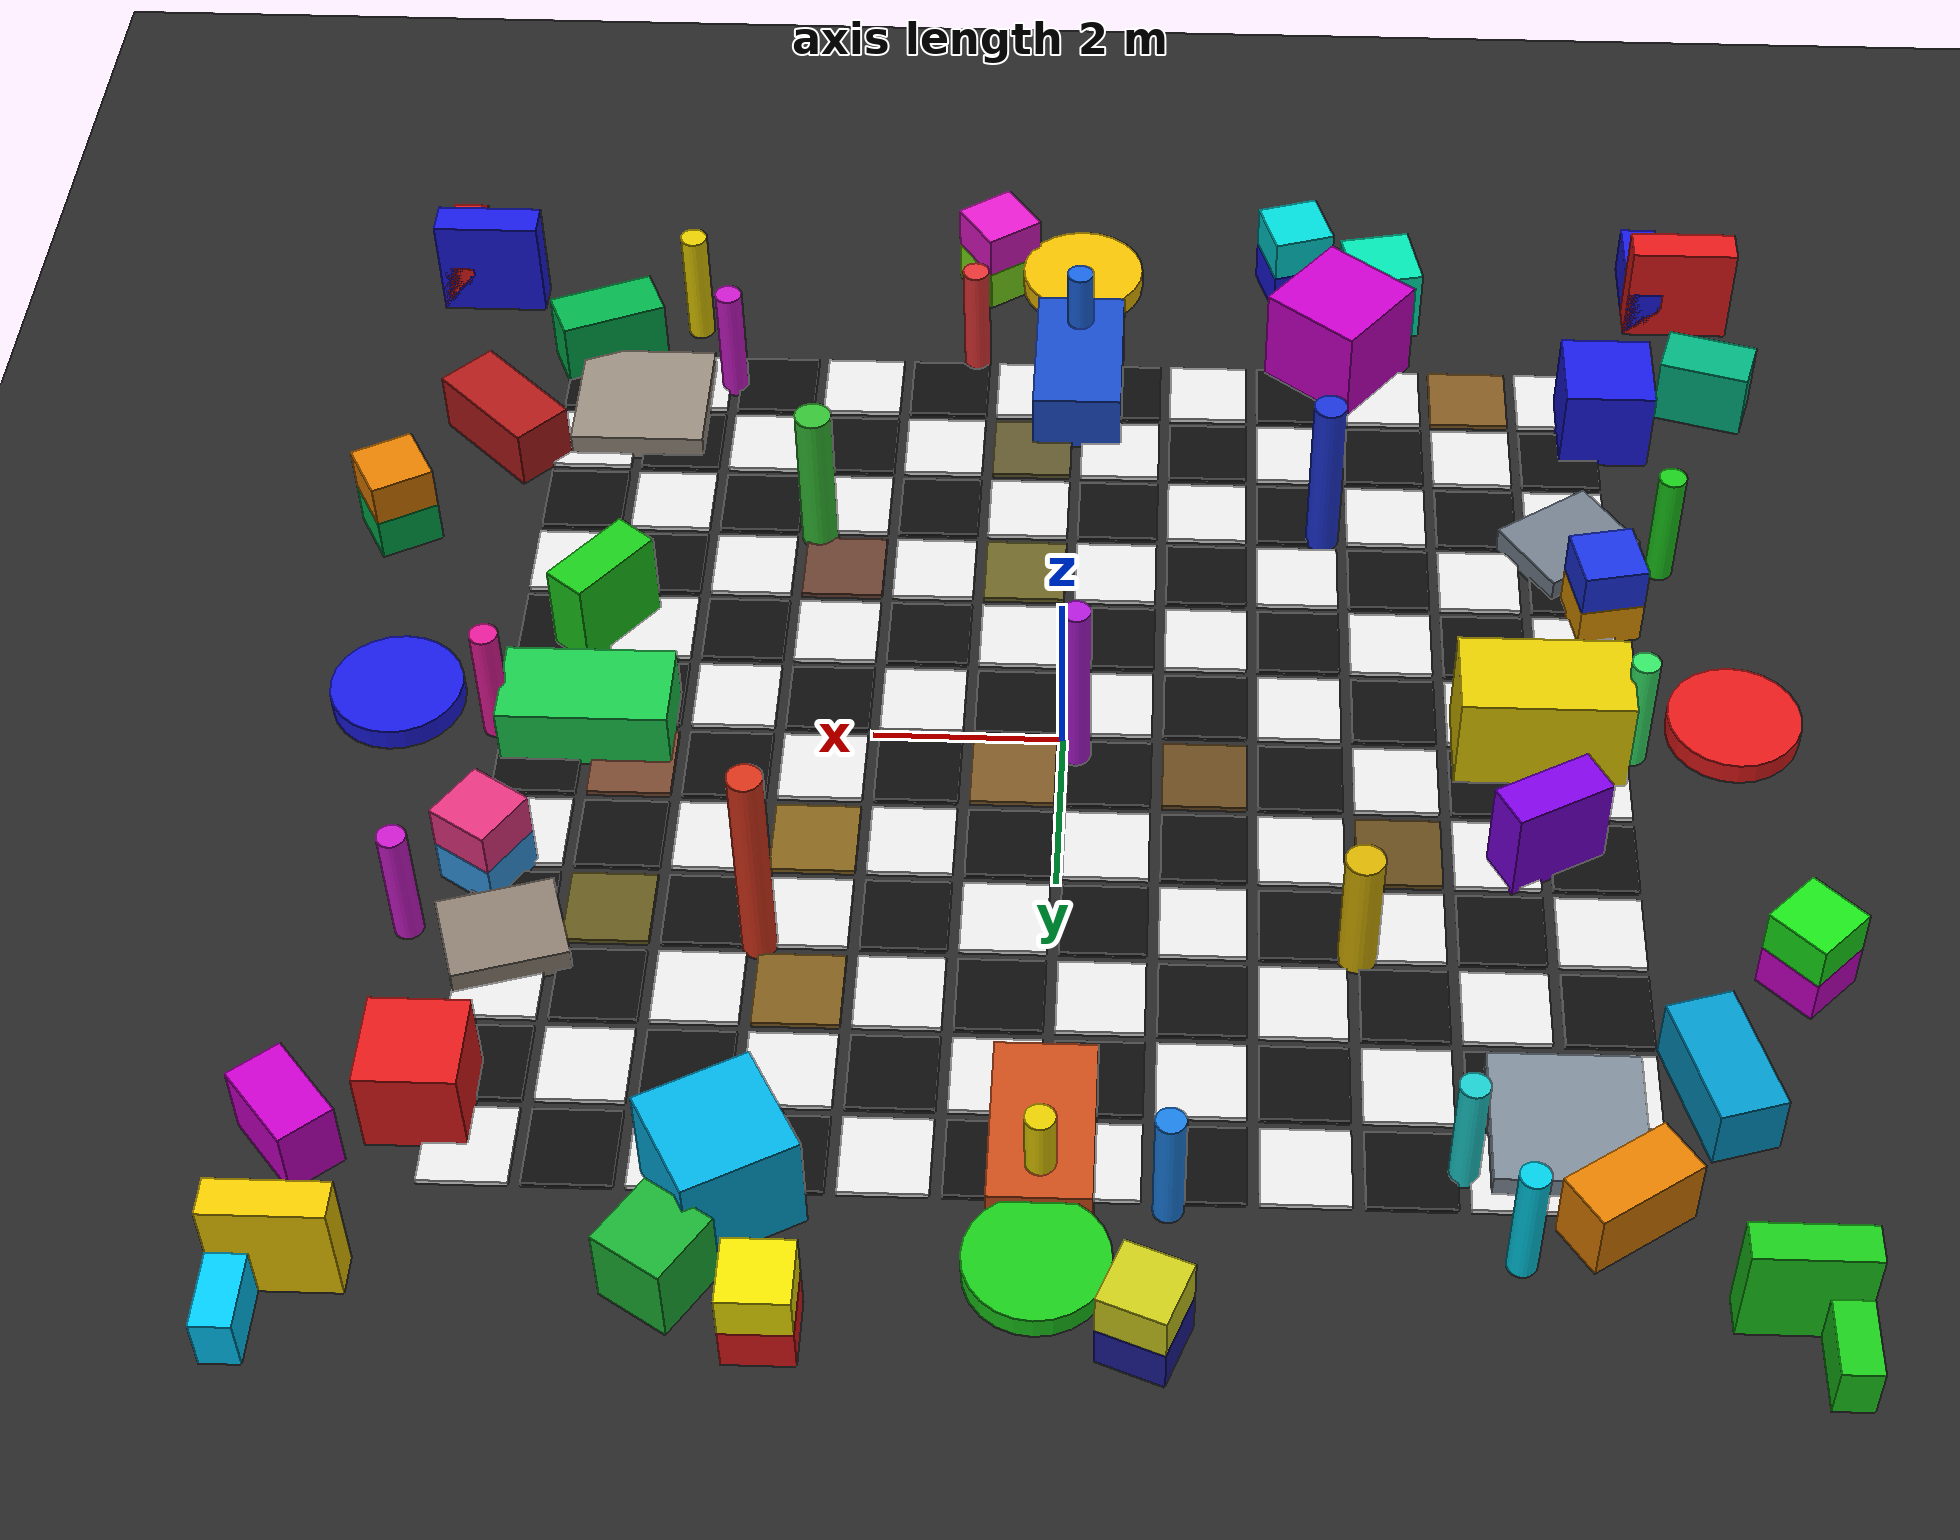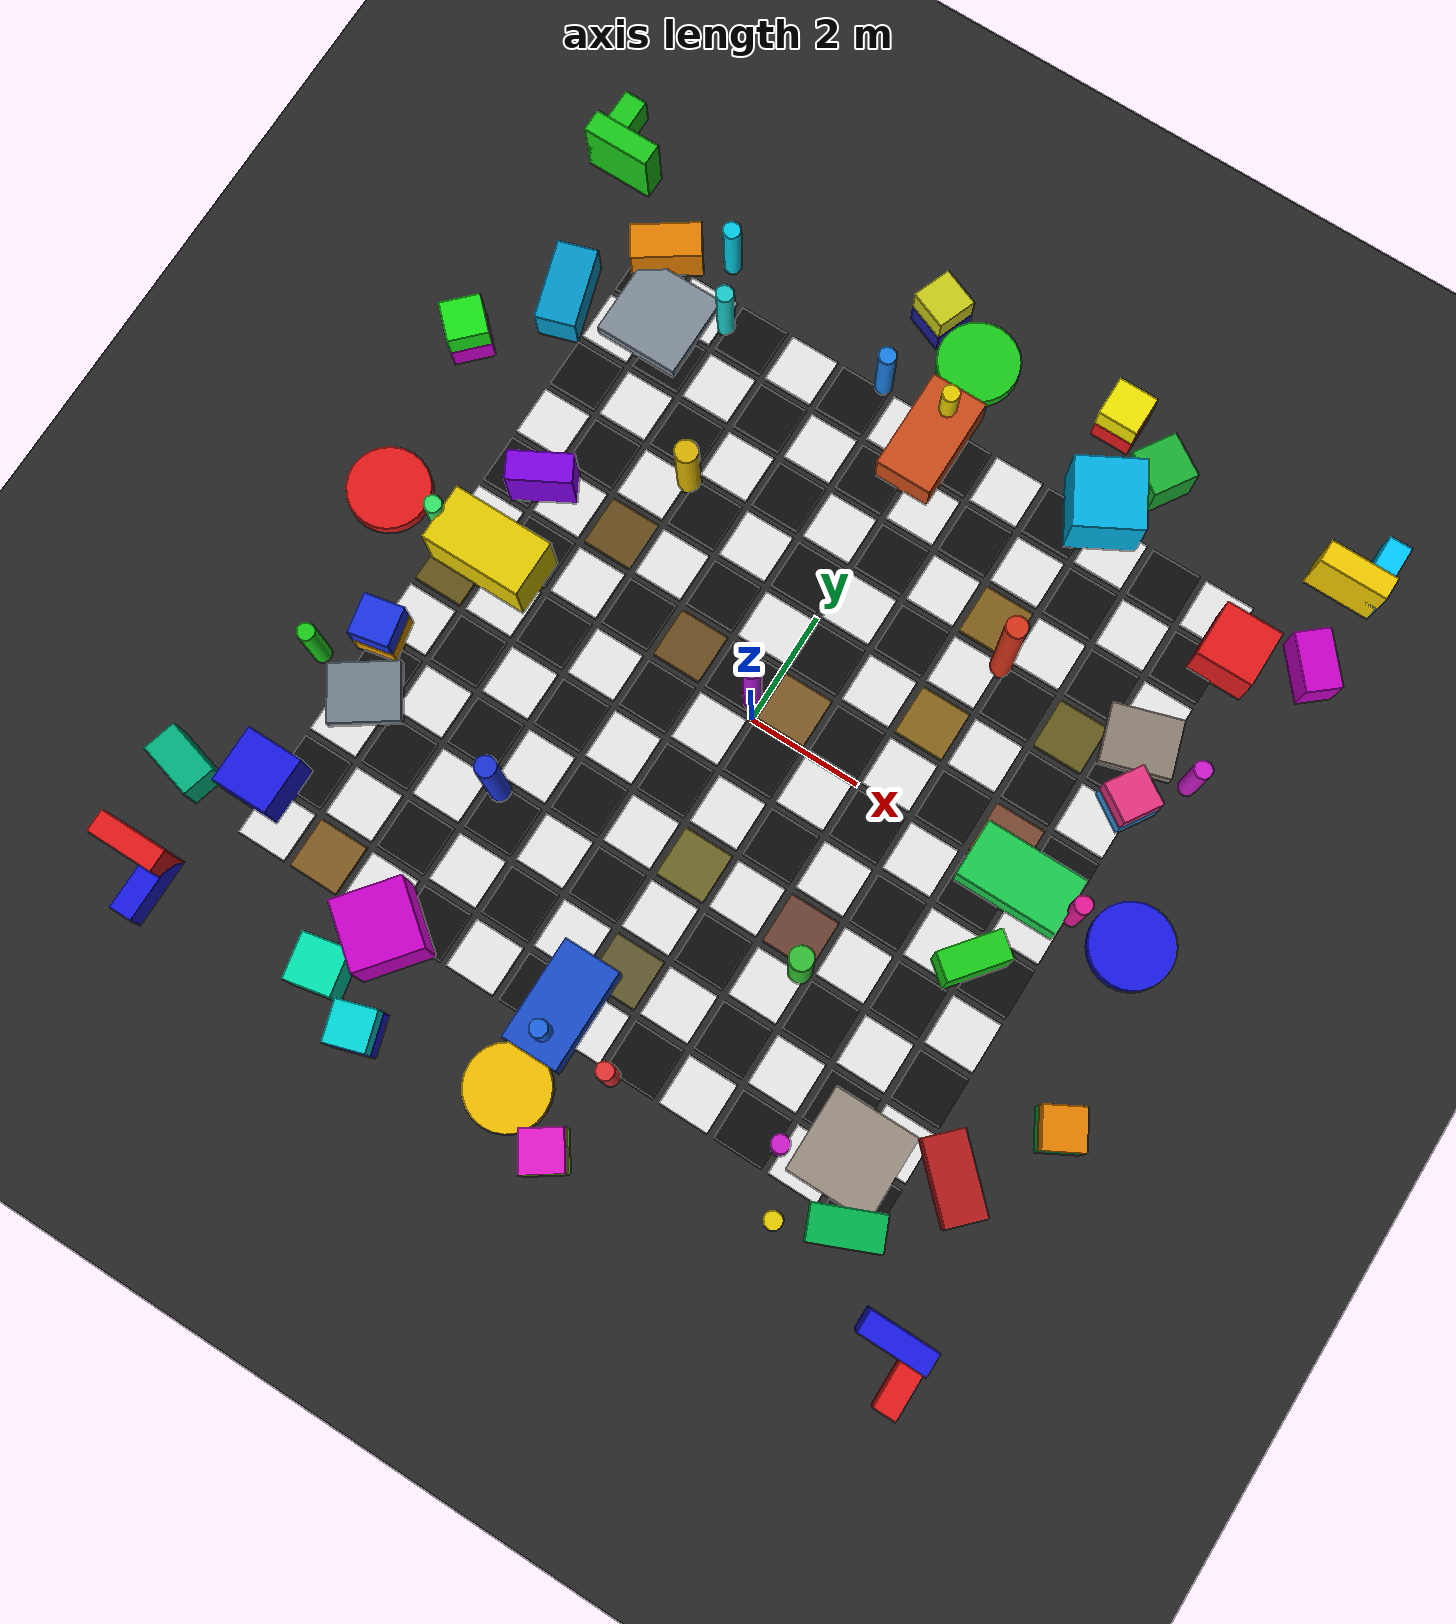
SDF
<sdf version="1.9">
 <world name="slam_world_v5_realistic">
  <plugin filename="gz-sim-physics-system" name="gz::sim::systems::Physics"/>
  <plugin filename="gz-sim-user-commands-system" name="gz::sim::systems::UserCommands"/>
  <plugin filename="gz-sim-scene-broadcaster-system" name="gz::sim::systems::SceneBroadcaster"/>
  <plugin filename="gz-sim-sensors-system" name="gz::sim::systems::Sensors">
   <render_engine>ogre2</render_engine>
  </plugin>
  <gravity>0 0 -9.8</gravity>
  <scene>
   <ambient>0.20 0.20 0.20 1</ambient>
   <background>0.45 0.60 0.80 1</background>
   <shadows>true</shadows>
  </scene>
  <light name="sun" type="directional">
   <pose>0 0 30 0 0 0</pose>
   <diffuse>1.0 0.97 0.90 1</diffuse>
   <specular>0.55 0.55 0.50 1</specular>
   <direction>0.223 0.110 -1.000</direction>
  </light>
  <light name="fill_light" type="directional">
   <pose>0 0 20 0 0 0</pose>
   <diffuse>0.25 0.27 0.30 1</diffuse>
   <specular>0.04 0.04 0.04 1</specular>
   <direction>-0.223 -0.110 -1.000</direction>
   <cast_shadows>false</cast_shadows>
  </light>
  <light name="rim_light" type="directional">
   <pose>0 0 15 0 0 0</pose>
   <diffuse>0.15 0.18 0.22 1</diffuse>
   <specular>0.10 0.10 0.12 1</specular>
   <direction>0.110 -0.223 -0.500</direction>
   <cast_shadows>false</cast_shadows>
  </light>
  <model name="ground_plane">
   <static>true</static>
   <link name="ground_link">
    <collision name="collision">
     <geometry><plane><normal>0 0 1</normal><size>80 80</size></plane></geometry>
    </collision>
    <visual name="visual">
     <geometry><plane><normal>0 0 1</normal><size>80 80</size></plane></geometry>
     <material>
      <ambient>0.12 0.12 0.12 1</ambient>
      <diffuse>0.15 0.15 0.15 1</diffuse>
      <specular>0.02 0.02 0.02 1</specular>
     </material>
    </visual>
   </link>
  </model>
  <model name="cb_0">
   <static>true</static>
   <pose>-5.500 -5.500 0.030 0 0 0</pose>
   <link name="link">
    <collision name="col"><geometry><box><size>0.880 0.880 0.060</size></box></geometry></collision>
    <visual name="vis">
     <geometry><box><size>0.880 0.880 0.060</size></box></geometry>
     <material>
      <ambient>0.910 0.910 0.910 1</ambient>
      <diffuse>0.910 0.910 0.910 1</diffuse>
      <specular>0.080 0.080 0.080 1</specular>
     </material>
    </visual>
   </link>
  </model>
  <model name="cb_1">
   <static>true</static>
   <pose>-5.500 -4.500 0.030 0 0 0</pose>
   <link name="link">
    <collision name="col"><geometry><box><size>0.880 0.880 0.060</size></box></geometry></collision>
    <visual name="vis">
     <geometry><box><size>0.880 0.880 0.060</size></box></geometry>
     <material>
      <ambient>0.050 0.050 0.050 1</ambient>
      <diffuse>0.050 0.050 0.050 1</diffuse>
      <specular>0.020 0.020 0.020 1</specular>
     </material>
    </visual>
   </link>
  </model>
  <model name="cb_2">
   <static>true</static>
   <pose>-5.500 -3.500 0.030 0 0 0</pose>
   <link name="link">
    <collision name="col"><geometry><box><size>0.880 0.880 0.060</size></box></geometry></collision>
    <visual name="vis">
     <geometry><box><size>0.880 0.880 0.060</size></box></geometry>
     <material>
      <ambient>0.910 0.910 0.910 1</ambient>
      <diffuse>0.910 0.910 0.910 1</diffuse>
      <specular>0.080 0.080 0.080 1</specular>
     </material>
    </visual>
   </link>
  </model>
  <model name="cb_3">
   <static>true</static>
   <pose>-5.500 -2.500 0.030 0 0 0</pose>
   <link name="link">
    <collision name="col"><geometry><box><size>0.880 0.880 0.060</size></box></geometry></collision>
    <visual name="vis">
     <geometry><box><size>0.880 0.880 0.060</size></box></geometry>
     <material>
      <ambient>0.050 0.050 0.050 1</ambient>
      <diffuse>0.050 0.050 0.050 1</diffuse>
      <specular>0.020 0.020 0.020 1</specular>
     </material>
    </visual>
   </link>
  </model>
  <model name="cb_4">
   <static>true</static>
   <pose>-5.500 -1.500 0.030 0 0 0</pose>
   <link name="link">
    <collision name="col"><geometry><box><size>0.880 0.880 0.060</size></box></geometry></collision>
    <visual name="vis">
     <geometry><box><size>0.880 0.880 0.060</size></box></geometry>
     <material>
      <ambient>0.910 0.910 0.910 1</ambient>
      <diffuse>0.910 0.910 0.910 1</diffuse>
      <specular>0.080 0.080 0.080 1</specular>
     </material>
    </visual>
   </link>
  </model>
  <model name="cb_5">
   <static>true</static>
   <pose>-5.500 -0.500 0.030 0 0 0</pose>
   <link name="link">
    <collision name="col"><geometry><box><size>0.880 0.880 0.060</size></box></geometry></collision>
    <visual name="vis">
     <geometry><box><size>0.880 0.880 0.060</size></box></geometry>
     <material>
      <ambient>0.394 0.326 0.103 1</ambient>
      <diffuse>0.394 0.326 0.103 1</diffuse>
      <specular>0.020 0.020 0.020 1</specular>
     </material>
    </visual>
   </link>
  </model>
  <model name="cb_6">
   <static>true</static>
   <pose>-5.500 0.500 0.030 0 0 0</pose>
   <link name="link">
    <collision name="col"><geometry><box><size>0.880 0.880 0.060</size></box></geometry></collision>
    <visual name="vis">
     <geometry><box><size>0.880 0.880 0.060</size></box></geometry>
     <material>
      <ambient>0.910 0.910 0.910 1</ambient>
      <diffuse>0.910 0.910 0.910 1</diffuse>
      <specular>0.080 0.080 0.080 1</specular>
     </material>
    </visual>
   </link>
  </model>
  <model name="cb_7">
   <static>true</static>
   <pose>-5.500 1.500 0.030 0 0 0</pose>
   <link name="link">
    <collision name="col"><geometry><box><size>0.880 0.880 0.060</size></box></geometry></collision>
    <visual name="vis">
     <geometry><box><size>0.880 0.880 0.060</size></box></geometry>
     <material>
      <ambient>0.050 0.050 0.050 1</ambient>
      <diffuse>0.050 0.050 0.050 1</diffuse>
      <specular>0.020 0.020 0.020 1</specular>
     </material>
    </visual>
   </link>
  </model>
  <model name="cb_8">
   <static>true</static>
   <pose>-5.500 2.500 0.030 0 0 0</pose>
   <link name="link">
    <collision name="col"><geometry><box><size>0.880 0.880 0.060</size></box></geometry></collision>
    <visual name="vis">
     <geometry><box><size>0.880 0.880 0.060</size></box></geometry>
     <material>
      <ambient>0.910 0.910 0.910 1</ambient>
      <diffuse>0.910 0.910 0.910 1</diffuse>
      <specular>0.080 0.080 0.080 1</specular>
     </material>
    </visual>
   </link>
  </model>
  <model name="cb_9">
   <static>true</static>
   <pose>-5.500 3.500 0.030 0 0 0</pose>
   <link name="link">
    <collision name="col"><geometry><box><size>0.880 0.880 0.060</size></box></geometry></collision>
    <visual name="vis">
     <geometry><box><size>0.880 0.880 0.060</size></box></geometry>
     <material>
      <ambient>0.050 0.050 0.050 1</ambient>
      <diffuse>0.050 0.050 0.050 1</diffuse>
      <specular>0.020 0.020 0.020 1</specular>
     </material>
    </visual>
   </link>
  </model>
  <model name="cb_10">
   <static>true</static>
   <pose>-5.500 4.500 0.030 0 0 0</pose>
   <link name="link">
    <collision name="col"><geometry><box><size>0.880 0.880 0.060</size></box></geometry></collision>
    <visual name="vis">
     <geometry><box><size>0.880 0.880 0.060</size></box></geometry>
     <material>
      <ambient>0.910 0.910 0.910 1</ambient>
      <diffuse>0.910 0.910 0.910 1</diffuse>
      <specular>0.080 0.080 0.080 1</specular>
     </material>
    </visual>
   </link>
  </model>
  <model name="cb_11">
   <static>true</static>
   <pose>-5.500 5.500 0.030 0 0 0</pose>
   <link name="link">
    <collision name="col"><geometry><box><size>0.880 0.880 0.060</size></box></geometry></collision>
    <visual name="vis">
     <geometry><box><size>0.880 0.880 0.060</size></box></geometry>
     <material>
      <ambient>0.050 0.050 0.050 1</ambient>
      <diffuse>0.050 0.050 0.050 1</diffuse>
      <specular>0.020 0.020 0.020 1</specular>
     </material>
    </visual>
   </link>
  </model>
  <model name="cb_12">
   <static>true</static>
   <pose>-4.500 -5.500 0.030 0 0 0</pose>
   <link name="link">
    <collision name="col"><geometry><box><size>0.880 0.880 0.060</size></box></geometry></collision>
    <visual name="vis">
     <geometry><box><size>0.880 0.880 0.060</size></box></geometry>
     <material>
      <ambient>0.511 0.355 0.134 1</ambient>
      <diffuse>0.511 0.355 0.134 1</diffuse>
      <specular>0.020 0.020 0.020 1</specular>
     </material>
    </visual>
   </link>
  </model>
  <model name="cb_13">
   <static>true</static>
   <pose>-4.500 -4.500 0.030 0 0 0</pose>
   <link name="link">
    <collision name="col"><geometry><box><size>0.880 0.880 0.060</size></box></geometry></collision>
    <visual name="vis">
     <geometry><box><size>0.880 0.880 0.060</size></box></geometry>
     <material>
      <ambient>0.910 0.910 0.910 1</ambient>
      <diffuse>0.910 0.910 0.910 1</diffuse>
      <specular>0.080 0.080 0.080 1</specular>
     </material>
    </visual>
   </link>
  </model>
  <model name="cb_14">
   <static>true</static>
   <pose>-4.500 -3.500 0.030 0 0 0</pose>
   <link name="link">
    <collision name="col"><geometry><box><size>0.880 0.880 0.060</size></box></geometry></collision>
    <visual name="vis">
     <geometry><box><size>0.880 0.880 0.060</size></box></geometry>
     <material>
      <ambient>0.050 0.050 0.050 1</ambient>
      <diffuse>0.050 0.050 0.050 1</diffuse>
      <specular>0.020 0.020 0.020 1</specular>
     </material>
    </visual>
   </link>
  </model>
  <model name="cb_15">
   <static>true</static>
   <pose>-4.500 -2.500 0.030 0 0 0</pose>
   <link name="link">
    <collision name="col"><geometry><box><size>0.880 0.880 0.060</size></box></geometry></collision>
    <visual name="vis">
     <geometry><box><size>0.880 0.880 0.060</size></box></geometry>
     <material>
      <ambient>0.910 0.910 0.910 1</ambient>
      <diffuse>0.910 0.910 0.910 1</diffuse>
      <specular>0.080 0.080 0.080 1</specular>
     </material>
    </visual>
   </link>
  </model>
  <model name="cb_16">
   <static>true</static>
   <pose>-4.500 -1.500 0.030 0 0 0</pose>
   <link name="link">
    <collision name="col"><geometry><box><size>0.880 0.880 0.060</size></box></geometry></collision>
    <visual name="vis">
     <geometry><box><size>0.880 0.880 0.060</size></box></geometry>
     <material>
      <ambient>0.050 0.050 0.050 1</ambient>
      <diffuse>0.050 0.050 0.050 1</diffuse>
      <specular>0.020 0.020 0.020 1</specular>
     </material>
    </visual>
   </link>
  </model>
  <model name="cb_17">
   <static>true</static>
   <pose>-4.500 -0.500 0.030 0 0 0</pose>
   <link name="link">
    <collision name="col"><geometry><box><size>0.880 0.880 0.060</size></box></geometry></collision>
    <visual name="vis">
     <geometry><box><size>0.880 0.880 0.060</size></box></geometry>
     <material>
      <ambient>0.910 0.910 0.910 1</ambient>
      <diffuse>0.910 0.910 0.910 1</diffuse>
      <specular>0.080 0.080 0.080 1</specular>
     </material>
    </visual>
   </link>
  </model>
  <model name="cb_18">
   <static>true</static>
   <pose>-4.500 0.500 0.030 0 0 0</pose>
   <link name="link">
    <collision name="col"><geometry><box><size>0.880 0.880 0.060</size></box></geometry></collision>
    <visual name="vis">
     <geometry><box><size>0.880 0.880 0.060</size></box></geometry>
     <material>
      <ambient>0.050 0.050 0.050 1</ambient>
      <diffuse>0.050 0.050 0.050 1</diffuse>
      <specular>0.020 0.020 0.020 1</specular>
     </material>
    </visual>
   </link>
  </model>
  <model name="cb_19">
   <static>true</static>
   <pose>-4.500 1.500 0.030 0 0 0</pose>
   <link name="link">
    <collision name="col"><geometry><box><size>0.880 0.880 0.060</size></box></geometry></collision>
    <visual name="vis">
     <geometry><box><size>0.880 0.880 0.060</size></box></geometry>
     <material>
      <ambient>0.910 0.910 0.910 1</ambient>
      <diffuse>0.910 0.910 0.910 1</diffuse>
      <specular>0.080 0.080 0.080 1</specular>
     </material>
    </visual>
   </link>
  </model>
  <model name="cb_20">
   <static>true</static>
   <pose>-4.500 2.500 0.030 0 0 0</pose>
   <link name="link">
    <collision name="col"><geometry><box><size>0.880 0.880 0.060</size></box></geometry></collision>
    <visual name="vis">
     <geometry><box><size>0.880 0.880 0.060</size></box></geometry>
     <material>
      <ambient>0.050 0.050 0.050 1</ambient>
      <diffuse>0.050 0.050 0.050 1</diffuse>
      <specular>0.020 0.020 0.020 1</specular>
     </material>
    </visual>
   </link>
  </model>
  <model name="cb_21">
   <static>true</static>
   <pose>-4.500 3.500 0.030 0 0 0</pose>
   <link name="link">
    <collision name="col"><geometry><box><size>0.880 0.880 0.060</size></box></geometry></collision>
    <visual name="vis">
     <geometry><box><size>0.880 0.880 0.060</size></box></geometry>
     <material>
      <ambient>0.910 0.910 0.910 1</ambient>
      <diffuse>0.910 0.910 0.910 1</diffuse>
      <specular>0.080 0.080 0.080 1</specular>
     </material>
    </visual>
   </link>
  </model>
  <model name="cb_22">
   <static>true</static>
   <pose>-4.500 4.500 0.030 0 0 0</pose>
   <link name="link">
    <collision name="col"><geometry><box><size>0.880 0.880 0.060</size></box></geometry></collision>
    <visual name="vis">
     <geometry><box><size>0.880 0.880 0.060</size></box></geometry>
     <material>
      <ambient>0.050 0.050 0.050 1</ambient>
      <diffuse>0.050 0.050 0.050 1</diffuse>
      <specular>0.020 0.020 0.020 1</specular>
     </material>
    </visual>
   </link>
  </model>
  <model name="cb_23">
   <static>true</static>
   <pose>-4.500 5.500 0.030 0 0 0</pose>
   <link name="link">
    <collision name="col"><geometry><box><size>0.880 0.880 0.060</size></box></geometry></collision>
    <visual name="vis">
     <geometry><box><size>0.880 0.880 0.060</size></box></geometry>
     <material>
      <ambient>0.910 0.910 0.910 1</ambient>
      <diffuse>0.910 0.910 0.910 1</diffuse>
      <specular>0.080 0.080 0.080 1</specular>
     </material>
    </visual>
   </link>
  </model>
  <model name="cb_24">
   <static>true</static>
   <pose>-3.500 -5.500 0.030 0 0 0</pose>
   <link name="link">
    <collision name="col"><geometry><box><size>0.880 0.880 0.060</size></box></geometry></collision>
    <visual name="vis">
     <geometry><box><size>0.880 0.880 0.060</size></box></geometry>
     <material>
      <ambient>0.910 0.910 0.910 1</ambient>
      <diffuse>0.910 0.910 0.910 1</diffuse>
      <specular>0.080 0.080 0.080 1</specular>
     </material>
    </visual>
   </link>
  </model>
  <model name="cb_25">
   <static>true</static>
   <pose>-3.500 -4.500 0.030 0 0 0</pose>
   <link name="link">
    <collision name="col"><geometry><box><size>0.880 0.880 0.060</size></box></geometry></collision>
    <visual name="vis">
     <geometry><box><size>0.880 0.880 0.060</size></box></geometry>
     <material>
      <ambient>0.050 0.050 0.050 1</ambient>
      <diffuse>0.050 0.050 0.050 1</diffuse>
      <specular>0.020 0.020 0.020 1</specular>
     </material>
    </visual>
   </link>
  </model>
  <model name="cb_26">
   <static>true</static>
   <pose>-3.500 -3.500 0.030 0 0 0</pose>
   <link name="link">
    <collision name="col"><geometry><box><size>0.880 0.880 0.060</size></box></geometry></collision>
    <visual name="vis">
     <geometry><box><size>0.880 0.880 0.060</size></box></geometry>
     <material>
      <ambient>0.910 0.910 0.910 1</ambient>
      <diffuse>0.910 0.910 0.910 1</diffuse>
      <specular>0.080 0.080 0.080 1</specular>
     </material>
    </visual>
   </link>
  </model>
  <model name="cb_27">
   <static>true</static>
   <pose>-3.500 -2.500 0.030 0 0 0</pose>
   <link name="link">
    <collision name="col"><geometry><box><size>0.880 0.880 0.060</size></box></geometry></collision>
    <visual name="vis">
     <geometry><box><size>0.880 0.880 0.060</size></box></geometry>
     <material>
      <ambient>0.050 0.050 0.050 1</ambient>
      <diffuse>0.050 0.050 0.050 1</diffuse>
      <specular>0.020 0.020 0.020 1</specular>
     </material>
    </visual>
   </link>
  </model>
  <model name="cb_28">
   <static>true</static>
   <pose>-3.500 -1.500 0.030 0 0 0</pose>
   <link name="link">
    <collision name="col"><geometry><box><size>0.880 0.880 0.060</size></box></geometry></collision>
    <visual name="vis">
     <geometry><box><size>0.880 0.880 0.060</size></box></geometry>
     <material>
      <ambient>0.910 0.910 0.910 1</ambient>
      <diffuse>0.910 0.910 0.910 1</diffuse>
      <specular>0.080 0.080 0.080 1</specular>
     </material>
    </visual>
   </link>
  </model>
  <model name="cb_29">
   <static>true</static>
   <pose>-3.500 -0.500 0.030 0 0 0</pose>
   <link name="link">
    <collision name="col"><geometry><box><size>0.880 0.880 0.060</size></box></geometry></collision>
    <visual name="vis">
     <geometry><box><size>0.880 0.880 0.060</size></box></geometry>
     <material>
      <ambient>0.050 0.050 0.050 1</ambient>
      <diffuse>0.050 0.050 0.050 1</diffuse>
      <specular>0.020 0.020 0.020 1</specular>
     </material>
    </visual>
   </link>
  </model>
  <model name="cb_30">
   <static>true</static>
   <pose>-3.500 0.500 0.030 0 0 0</pose>
   <link name="link">
    <collision name="col"><geometry><box><size>0.880 0.880 0.060</size></box></geometry></collision>
    <visual name="vis">
     <geometry><box><size>0.880 0.880 0.060</size></box></geometry>
     <material>
      <ambient>0.910 0.910 0.910 1</ambient>
      <diffuse>0.910 0.910 0.910 1</diffuse>
      <specular>0.080 0.080 0.080 1</specular>
     </material>
    </visual>
   </link>
  </model>
  <model name="cb_31">
   <static>true</static>
   <pose>-3.500 1.500 0.030 0 0 0</pose>
   <link name="link">
    <collision name="col"><geometry><box><size>0.880 0.880 0.060</size></box></geometry></collision>
    <visual name="vis">
     <geometry><box><size>0.880 0.880 0.060</size></box></geometry>
     <material>
      <ambient>0.396 0.293 0.108 1</ambient>
      <diffuse>0.396 0.293 0.108 1</diffuse>
      <specular>0.020 0.020 0.020 1</specular>
     </material>
    </visual>
   </link>
  </model>
  <model name="cb_32">
   <static>true</static>
   <pose>-3.500 2.500 0.030 0 0 0</pose>
   <link name="link">
    <collision name="col"><geometry><box><size>0.880 0.880 0.060</size></box></geometry></collision>
    <visual name="vis">
     <geometry><box><size>0.880 0.880 0.060</size></box></geometry>
     <material>
      <ambient>0.910 0.910 0.910 1</ambient>
      <diffuse>0.910 0.910 0.910 1</diffuse>
      <specular>0.080 0.080 0.080 1</specular>
     </material>
    </visual>
   </link>
  </model>
  <model name="cb_33">
   <static>true</static>
   <pose>-3.500 3.500 0.030 0 0 0</pose>
   <link name="link">
    <collision name="col"><geometry><box><size>0.880 0.880 0.060</size></box></geometry></collision>
    <visual name="vis">
     <geometry><box><size>0.880 0.880 0.060</size></box></geometry>
     <material>
      <ambient>0.050 0.050 0.050 1</ambient>
      <diffuse>0.050 0.050 0.050 1</diffuse>
      <specular>0.020 0.020 0.020 1</specular>
     </material>
    </visual>
   </link>
  </model>
  <model name="cb_34">
   <static>true</static>
   <pose>-3.500 4.500 0.030 0 0 0</pose>
   <link name="link">
    <collision name="col"><geometry><box><size>0.880 0.880 0.060</size></box></geometry></collision>
    <visual name="vis">
     <geometry><box><size>0.880 0.880 0.060</size></box></geometry>
     <material>
      <ambient>0.910 0.910 0.910 1</ambient>
      <diffuse>0.910 0.910 0.910 1</diffuse>
      <specular>0.080 0.080 0.080 1</specular>
     </material>
    </visual>
   </link>
  </model>
  <model name="cb_35">
   <static>true</static>
   <pose>-3.500 5.500 0.030 0 0 0</pose>
   <link name="link">
    <collision name="col"><geometry><box><size>0.880 0.880 0.060</size></box></geometry></collision>
    <visual name="vis">
     <geometry><box><size>0.880 0.880 0.060</size></box></geometry>
     <material>
      <ambient>0.050 0.050 0.050 1</ambient>
      <diffuse>0.050 0.050 0.050 1</diffuse>
      <specular>0.020 0.020 0.020 1</specular>
     </material>
    </visual>
   </link>
  </model>
  <model name="cb_36">
   <static>true</static>
   <pose>-2.500 -5.500 0.030 0 0 0</pose>
   <link name="link">
    <collision name="col"><geometry><box><size>0.880 0.880 0.060</size></box></geometry></collision>
    <visual name="vis">
     <geometry><box><size>0.880 0.880 0.060</size></box></geometry>
     <material>
      <ambient>0.050 0.050 0.050 1</ambient>
      <diffuse>0.050 0.050 0.050 1</diffuse>
      <specular>0.020 0.020 0.020 1</specular>
     </material>
    </visual>
   </link>
  </model>
  <model name="cb_37">
   <static>true</static>
   <pose>-2.500 -4.500 0.030 0 0 0</pose>
   <link name="link">
    <collision name="col"><geometry><box><size>0.880 0.880 0.060</size></box></geometry></collision>
    <visual name="vis">
     <geometry><box><size>0.880 0.880 0.060</size></box></geometry>
     <material>
      <ambient>0.910 0.910 0.910 1</ambient>
      <diffuse>0.910 0.910 0.910 1</diffuse>
      <specular>0.080 0.080 0.080 1</specular>
     </material>
    </visual>
   </link>
  </model>
  <model name="cb_38">
   <static>true</static>
   <pose>-2.500 -3.500 0.030 0 0 0</pose>
   <link name="link">
    <collision name="col"><geometry><box><size>0.880 0.880 0.060</size></box></geometry></collision>
    <visual name="vis">
     <geometry><box><size>0.880 0.880 0.060</size></box></geometry>
     <material>
      <ambient>0.050 0.050 0.050 1</ambient>
      <diffuse>0.050 0.050 0.050 1</diffuse>
      <specular>0.020 0.020 0.020 1</specular>
     </material>
    </visual>
   </link>
  </model>
  <model name="cb_39">
   <static>true</static>
   <pose>-2.500 -2.500 0.030 0 0 0</pose>
   <link name="link">
    <collision name="col"><geometry><box><size>0.880 0.880 0.060</size></box></geometry></collision>
    <visual name="vis">
     <geometry><box><size>0.880 0.880 0.060</size></box></geometry>
     <material>
      <ambient>0.910 0.910 0.910 1</ambient>
      <diffuse>0.910 0.910 0.910 1</diffuse>
      <specular>0.080 0.080 0.080 1</specular>
     </material>
    </visual>
   </link>
  </model>
  <model name="cb_40">
   <static>true</static>
   <pose>-2.500 -1.500 0.030 0 0 0</pose>
   <link name="link">
    <collision name="col"><geometry><box><size>0.880 0.880 0.060</size></box></geometry></collision>
    <visual name="vis">
     <geometry><box><size>0.880 0.880 0.060</size></box></geometry>
     <material>
      <ambient>0.050 0.050 0.050 1</ambient>
      <diffuse>0.050 0.050 0.050 1</diffuse>
      <specular>0.020 0.020 0.020 1</specular>
     </material>
    </visual>
   </link>
  </model>
  <model name="cb_41">
   <static>true</static>
   <pose>-2.500 -0.500 0.030 0 0 0</pose>
   <link name="link">
    <collision name="col"><geometry><box><size>0.880 0.880 0.060</size></box></geometry></collision>
    <visual name="vis">
     <geometry><box><size>0.880 0.880 0.060</size></box></geometry>
     <material>
      <ambient>0.910 0.910 0.910 1</ambient>
      <diffuse>0.910 0.910 0.910 1</diffuse>
      <specular>0.080 0.080 0.080 1</specular>
     </material>
    </visual>
   </link>
  </model>
  <model name="cb_42">
   <static>true</static>
   <pose>-2.500 0.500 0.030 0 0 0</pose>
   <link name="link">
    <collision name="col"><geometry><box><size>0.880 0.880 0.060</size></box></geometry></collision>
    <visual name="vis">
     <geometry><box><size>0.880 0.880 0.060</size></box></geometry>
     <material>
      <ambient>0.050 0.050 0.050 1</ambient>
      <diffuse>0.050 0.050 0.050 1</diffuse>
      <specular>0.020 0.020 0.020 1</specular>
     </material>
    </visual>
   </link>
  </model>
  <model name="cb_43">
   <static>true</static>
   <pose>-2.500 1.500 0.030 0 0 0</pose>
   <link name="link">
    <collision name="col"><geometry><box><size>0.880 0.880 0.060</size></box></geometry></collision>
    <visual name="vis">
     <geometry><box><size>0.880 0.880 0.060</size></box></geometry>
     <material>
      <ambient>0.910 0.910 0.910 1</ambient>
      <diffuse>0.910 0.910 0.910 1</diffuse>
      <specular>0.080 0.080 0.080 1</specular>
     </material>
    </visual>
   </link>
  </model>
  <model name="cb_44">
   <static>true</static>
   <pose>-2.500 2.500 0.030 0 0 0</pose>
   <link name="link">
    <collision name="col"><geometry><box><size>0.880 0.880 0.060</size></box></geometry></collision>
    <visual name="vis">
     <geometry><box><size>0.880 0.880 0.060</size></box></geometry>
     <material>
      <ambient>0.050 0.050 0.050 1</ambient>
      <diffuse>0.050 0.050 0.050 1</diffuse>
      <specular>0.020 0.020 0.020 1</specular>
     </material>
    </visual>
   </link>
  </model>
  <model name="cb_45">
   <static>true</static>
   <pose>-2.500 3.500 0.030 0 0 0</pose>
   <link name="link">
    <collision name="col"><geometry><box><size>0.880 0.880 0.060</size></box></geometry></collision>
    <visual name="vis">
     <geometry><box><size>0.880 0.880 0.060</size></box></geometry>
     <material>
      <ambient>0.910 0.910 0.910 1</ambient>
      <diffuse>0.910 0.910 0.910 1</diffuse>
      <specular>0.080 0.080 0.080 1</specular>
     </material>
    </visual>
   </link>
  </model>
  <model name="cb_46">
   <static>true</static>
   <pose>-2.500 4.500 0.030 0 0 0</pose>
   <link name="link">
    <collision name="col"><geometry><box><size>0.880 0.880 0.060</size></box></geometry></collision>
    <visual name="vis">
     <geometry><box><size>0.880 0.880 0.060</size></box></geometry>
     <material>
      <ambient>0.050 0.050 0.050 1</ambient>
      <diffuse>0.050 0.050 0.050 1</diffuse>
      <specular>0.020 0.020 0.020 1</specular>
     </material>
    </visual>
   </link>
  </model>
  <model name="cb_47">
   <static>true</static>
   <pose>-2.500 5.500 0.030 0 0 0</pose>
   <link name="link">
    <collision name="col"><geometry><box><size>0.880 0.880 0.060</size></box></geometry></collision>
    <visual name="vis">
     <geometry><box><size>0.880 0.880 0.060</size></box></geometry>
     <material>
      <ambient>0.910 0.910 0.910 1</ambient>
      <diffuse>0.910 0.910 0.910 1</diffuse>
      <specular>0.080 0.080 0.080 1</specular>
     </material>
    </visual>
   </link>
  </model>
  <model name="cb_48">
   <static>true</static>
   <pose>-1.500 -5.500 0.030 0 0 0</pose>
   <link name="link">
    <collision name="col"><geometry><box><size>0.880 0.880 0.060</size></box></geometry></collision>
    <visual name="vis">
     <geometry><box><size>0.880 0.880 0.060</size></box></geometry>
     <material>
      <ambient>0.910 0.910 0.910 1</ambient>
      <diffuse>0.910 0.910 0.910 1</diffuse>
      <specular>0.080 0.080 0.080 1</specular>
     </material>
    </visual>
   </link>
  </model>
  <model name="cb_49">
   <static>true</static>
   <pose>-1.500 -4.500 0.030 0 0 0</pose>
   <link name="link">
    <collision name="col"><geometry><box><size>0.880 0.880 0.060</size></box></geometry></collision>
    <visual name="vis">
     <geometry><box><size>0.880 0.880 0.060</size></box></geometry>
     <material>
      <ambient>0.050 0.050 0.050 1</ambient>
      <diffuse>0.050 0.050 0.050 1</diffuse>
      <specular>0.020 0.020 0.020 1</specular>
     </material>
    </visual>
   </link>
  </model>
  <model name="cb_50">
   <static>true</static>
   <pose>-1.500 -3.500 0.030 0 0 0</pose>
   <link name="link">
    <collision name="col"><geometry><box><size>0.880 0.880 0.060</size></box></geometry></collision>
    <visual name="vis">
     <geometry><box><size>0.880 0.880 0.060</size></box></geometry>
     <material>
      <ambient>0.910 0.910 0.910 1</ambient>
      <diffuse>0.910 0.910 0.910 1</diffuse>
      <specular>0.080 0.080 0.080 1</specular>
     </material>
    </visual>
   </link>
  </model>
  <model name="cb_51">
   <static>true</static>
   <pose>-1.500 -2.500 0.030 0 0 0</pose>
   <link name="link">
    <collision name="col"><geometry><box><size>0.880 0.880 0.060</size></box></geometry></collision>
    <visual name="vis">
     <geometry><box><size>0.880 0.880 0.060</size></box></geometry>
     <material>
      <ambient>0.050 0.050 0.050 1</ambient>
      <diffuse>0.050 0.050 0.050 1</diffuse>
      <specular>0.020 0.020 0.020 1</specular>
     </material>
    </visual>
   </link>
  </model>
  <model name="cb_52">
   <static>true</static>
   <pose>-1.500 -1.500 0.030 0 0 0</pose>
   <link name="link">
    <collision name="col"><geometry><box><size>0.880 0.880 0.060</size></box></geometry></collision>
    <visual name="vis">
     <geometry><box><size>0.880 0.880 0.060</size></box></geometry>
     <material>
      <ambient>0.910 0.910 0.910 1</ambient>
      <diffuse>0.910 0.910 0.910 1</diffuse>
      <specular>0.080 0.080 0.080 1</specular>
     </material>
    </visual>
   </link>
  </model>
  <model name="cb_53">
   <static>true</static>
   <pose>-1.500 -0.500 0.030 0 0 0</pose>
   <link name="link">
    <collision name="col"><geometry><box><size>0.880 0.880 0.060</size></box></geometry></collision>
    <visual name="vis">
     <geometry><box><size>0.880 0.880 0.060</size></box></geometry>
     <material>
      <ambient>0.050 0.050 0.050 1</ambient>
      <diffuse>0.050 0.050 0.050 1</diffuse>
      <specular>0.020 0.020 0.020 1</specular>
     </material>
    </visual>
   </link>
  </model>
  <model name="cb_54">
   <static>true</static>
   <pose>-1.500 0.500 0.030 0 0 0</pose>
   <link name="link">
    <collision name="col"><geometry><box><size>0.880 0.880 0.060</size></box></geometry></collision>
    <visual name="vis">
     <geometry><box><size>0.880 0.880 0.060</size></box></geometry>
     <material>
      <ambient>0.413 0.290 0.121 1</ambient>
      <diffuse>0.413 0.290 0.121 1</diffuse>
      <specular>0.020 0.020 0.020 1</specular>
     </material>
    </visual>
   </link>
  </model>
  <model name="cb_55">
   <static>true</static>
   <pose>-1.500 1.500 0.030 0 0 0</pose>
   <link name="link">
    <collision name="col"><geometry><box><size>0.880 0.880 0.060</size></box></geometry></collision>
    <visual name="vis">
     <geometry><box><size>0.880 0.880 0.060</size></box></geometry>
     <material>
      <ambient>0.050 0.050 0.050 1</ambient>
      <diffuse>0.050 0.050 0.050 1</diffuse>
      <specular>0.020 0.020 0.020 1</specular>
     </material>
    </visual>
   </link>
  </model>
  <model name="cb_56">
   <static>true</static>
   <pose>-1.500 2.500 0.030 0 0 0</pose>
   <link name="link">
    <collision name="col"><geometry><box><size>0.880 0.880 0.060</size></box></geometry></collision>
    <visual name="vis">
     <geometry><box><size>0.880 0.880 0.060</size></box></geometry>
     <material>
      <ambient>0.910 0.910 0.910 1</ambient>
      <diffuse>0.910 0.910 0.910 1</diffuse>
      <specular>0.080 0.080 0.080 1</specular>
     </material>
    </visual>
   </link>
  </model>
  <model name="cb_57">
   <static>true</static>
   <pose>-1.500 3.500 0.030 0 0 0</pose>
   <link name="link">
    <collision name="col"><geometry><box><size>0.880 0.880 0.060</size></box></geometry></collision>
    <visual name="vis">
     <geometry><box><size>0.880 0.880 0.060</size></box></geometry>
     <material>
      <ambient>0.050 0.050 0.050 1</ambient>
      <diffuse>0.050 0.050 0.050 1</diffuse>
      <specular>0.020 0.020 0.020 1</specular>
     </material>
    </visual>
   </link>
  </model>
  <model name="cb_58">
   <static>true</static>
   <pose>-1.500 4.500 0.030 0 0 0</pose>
   <link name="link">
    <collision name="col"><geometry><box><size>0.880 0.880 0.060</size></box></geometry></collision>
    <visual name="vis">
     <geometry><box><size>0.880 0.880 0.060</size></box></geometry>
     <material>
      <ambient>0.910 0.910 0.910 1</ambient>
      <diffuse>0.910 0.910 0.910 1</diffuse>
      <specular>0.080 0.080 0.080 1</specular>
     </material>
    </visual>
   </link>
  </model>
  <model name="cb_59">
   <static>true</static>
   <pose>-1.500 5.500 0.030 0 0 0</pose>
   <link name="link">
    <collision name="col"><geometry><box><size>0.880 0.880 0.060</size></box></geometry></collision>
    <visual name="vis">
     <geometry><box><size>0.880 0.880 0.060</size></box></geometry>
     <material>
      <ambient>0.050 0.050 0.050 1</ambient>
      <diffuse>0.050 0.050 0.050 1</diffuse>
      <specular>0.020 0.020 0.020 1</specular>
     </material>
    </visual>
   </link>
  </model>
  <model name="cb_60">
   <static>true</static>
   <pose>-0.500 -5.500 0.030 0 0 0</pose>
   <link name="link">
    <collision name="col"><geometry><box><size>0.880 0.880 0.060</size></box></geometry></collision>
    <visual name="vis">
     <geometry><box><size>0.880 0.880 0.060</size></box></geometry>
     <material>
      <ambient>0.050 0.050 0.050 1</ambient>
      <diffuse>0.050 0.050 0.050 1</diffuse>
      <specular>0.020 0.020 0.020 1</specular>
     </material>
    </visual>
   </link>
  </model>
  <model name="cb_61">
   <static>true</static>
   <pose>-0.500 -4.500 0.030 0 0 0</pose>
   <link name="link">
    <collision name="col"><geometry><box><size>0.880 0.880 0.060</size></box></geometry></collision>
    <visual name="vis">
     <geometry><box><size>0.880 0.880 0.060</size></box></geometry>
     <material>
      <ambient>0.910 0.910 0.910 1</ambient>
      <diffuse>0.910 0.910 0.910 1</diffuse>
      <specular>0.080 0.080 0.080 1</specular>
     </material>
    </visual>
   </link>
  </model>
  <model name="cb_62">
   <static>true</static>
   <pose>-0.500 -3.500 0.030 0 0 0</pose>
   <link name="link">
    <collision name="col"><geometry><box><size>0.880 0.880 0.060</size></box></geometry></collision>
    <visual name="vis">
     <geometry><box><size>0.880 0.880 0.060</size></box></geometry>
     <material>
      <ambient>0.050 0.050 0.050 1</ambient>
      <diffuse>0.050 0.050 0.050 1</diffuse>
      <specular>0.020 0.020 0.020 1</specular>
     </material>
    </visual>
   </link>
  </model>
  <model name="cb_63">
   <static>true</static>
   <pose>-0.500 -2.500 0.030 0 0 0</pose>
   <link name="link">
    <collision name="col"><geometry><box><size>0.880 0.880 0.060</size></box></geometry></collision>
    <visual name="vis">
     <geometry><box><size>0.880 0.880 0.060</size></box></geometry>
     <material>
      <ambient>0.910 0.910 0.910 1</ambient>
      <diffuse>0.910 0.910 0.910 1</diffuse>
      <specular>0.080 0.080 0.080 1</specular>
     </material>
    </visual>
   </link>
  </model>
  <model name="cb_64">
   <static>true</static>
   <pose>-0.500 -1.500 0.030 0 0 0</pose>
   <link name="link">
    <collision name="col"><geometry><box><size>0.880 0.880 0.060</size></box></geometry></collision>
    <visual name="vis">
     <geometry><box><size>0.880 0.880 0.060</size></box></geometry>
     <material>
      <ambient>0.050 0.050 0.050 1</ambient>
      <diffuse>0.050 0.050 0.050 1</diffuse>
      <specular>0.020 0.020 0.020 1</specular>
     </material>
    </visual>
   </link>
  </model>
  <model name="cb_65">
   <static>true</static>
   <pose>-0.500 -0.500 0.030 0 0 0</pose>
   <link name="link">
    <collision name="col"><geometry><box><size>0.880 0.880 0.060</size></box></geometry></collision>
    <visual name="vis">
     <geometry><box><size>0.880 0.880 0.060</size></box></geometry>
     <material>
      <ambient>0.910 0.910 0.910 1</ambient>
      <diffuse>0.910 0.910 0.910 1</diffuse>
      <specular>0.080 0.080 0.080 1</specular>
     </material>
    </visual>
   </link>
  </model>
  <model name="cb_66">
   <static>true</static>
   <pose>-0.500 0.500 0.030 0 0 0</pose>
   <link name="link">
    <collision name="col"><geometry><box><size>0.880 0.880 0.060</size></box></geometry></collision>
    <visual name="vis">
     <geometry><box><size>0.880 0.880 0.060</size></box></geometry>
     <material>
      <ambient>0.050 0.050 0.050 1</ambient>
      <diffuse>0.050 0.050 0.050 1</diffuse>
      <specular>0.020 0.020 0.020 1</specular>
     </material>
    </visual>
   </link>
  </model>
  <model name="cb_67">
   <static>true</static>
   <pose>-0.500 1.500 0.030 0 0 0</pose>
   <link name="link">
    <collision name="col"><geometry><box><size>0.880 0.880 0.060</size></box></geometry></collision>
    <visual name="vis">
     <geometry><box><size>0.880 0.880 0.060</size></box></geometry>
     <material>
      <ambient>0.910 0.910 0.910 1</ambient>
      <diffuse>0.910 0.910 0.910 1</diffuse>
      <specular>0.080 0.080 0.080 1</specular>
     </material>
    </visual>
   </link>
  </model>
  <model name="cb_68">
   <static>true</static>
   <pose>-0.500 2.500 0.030 0 0 0</pose>
   <link name="link">
    <collision name="col"><geometry><box><size>0.880 0.880 0.060</size></box></geometry></collision>
    <visual name="vis">
     <geometry><box><size>0.880 0.880 0.060</size></box></geometry>
     <material>
      <ambient>0.050 0.050 0.050 1</ambient>
      <diffuse>0.050 0.050 0.050 1</diffuse>
      <specular>0.020 0.020 0.020 1</specular>
     </material>
    </visual>
   </link>
  </model>
  <model name="cb_69">
   <static>true</static>
   <pose>-0.500 3.500 0.030 0 0 0</pose>
   <link name="link">
    <collision name="col"><geometry><box><size>0.880 0.880 0.060</size></box></geometry></collision>
    <visual name="vis">
     <geometry><box><size>0.880 0.880 0.060</size></box></geometry>
     <material>
      <ambient>0.910 0.910 0.910 1</ambient>
      <diffuse>0.910 0.910 0.910 1</diffuse>
      <specular>0.080 0.080 0.080 1</specular>
     </material>
    </visual>
   </link>
  </model>
  <model name="cb_70">
   <static>true</static>
   <pose>-0.500 4.500 0.030 0 0 0</pose>
   <link name="link">
    <collision name="col"><geometry><box><size>0.880 0.880 0.060</size></box></geometry></collision>
    <visual name="vis">
     <geometry><box><size>0.880 0.880 0.060</size></box></geometry>
     <material>
      <ambient>0.050 0.050 0.050 1</ambient>
      <diffuse>0.050 0.050 0.050 1</diffuse>
      <specular>0.020 0.020 0.020 1</specular>
     </material>
    </visual>
   </link>
  </model>
  <model name="cb_71">
   <static>true</static>
   <pose>-0.500 5.500 0.030 0 0 0</pose>
   <link name="link">
    <collision name="col"><geometry><box><size>0.880 0.880 0.060</size></box></geometry></collision>
    <visual name="vis">
     <geometry><box><size>0.880 0.880 0.060</size></box></geometry>
     <material>
      <ambient>0.910 0.910 0.910 1</ambient>
      <diffuse>0.910 0.910 0.910 1</diffuse>
      <specular>0.080 0.080 0.080 1</specular>
     </material>
    </visual>
   </link>
  </model>
  <model name="cb_72">
   <static>true</static>
   <pose>0.500 -5.500 0.030 0 0 0</pose>
   <link name="link">
    <collision name="col"><geometry><box><size>0.880 0.880 0.060</size></box></geometry></collision>
    <visual name="vis">
     <geometry><box><size>0.880 0.880 0.060</size></box></geometry>
     <material>
      <ambient>0.910 0.910 0.910 1</ambient>
      <diffuse>0.910 0.910 0.910 1</diffuse>
      <specular>0.080 0.080 0.080 1</specular>
     </material>
    </visual>
   </link>
  </model>
  <model name="cb_73">
   <static>true</static>
   <pose>0.500 -4.500 0.030 0 0 0</pose>
   <link name="link">
    <collision name="col"><geometry><box><size>0.880 0.880 0.060</size></box></geometry></collision>
    <visual name="vis">
     <geometry><box><size>0.880 0.880 0.060</size></box></geometry>
     <material>
      <ambient>0.372 0.344 0.179 1</ambient>
      <diffuse>0.372 0.344 0.179 1</diffuse>
      <specular>0.020 0.020 0.020 1</specular>
     </material>
    </visual>
   </link>
  </model>
  <model name="cb_74">
   <static>true</static>
   <pose>0.500 -3.500 0.030 0 0 0</pose>
   <link name="link">
    <collision name="col"><geometry><box><size>0.880 0.880 0.060</size></box></geometry></collision>
    <visual name="vis">
     <geometry><box><size>0.880 0.880 0.060</size></box></geometry>
     <material>
      <ambient>0.910 0.910 0.910 1</ambient>
      <diffuse>0.910 0.910 0.910 1</diffuse>
      <specular>0.080 0.080 0.080 1</specular>
     </material>
    </visual>
   </link>
  </model>
  <model name="cb_75">
   <static>true</static>
   <pose>0.500 -2.500 0.030 0 0 0</pose>
   <link name="link">
    <collision name="col"><geometry><box><size>0.880 0.880 0.060</size></box></geometry></collision>
    <visual name="vis">
     <geometry><box><size>0.880 0.880 0.060</size></box></geometry>
     <material>
      <ambient>0.426 0.399 0.153 1</ambient>
      <diffuse>0.426 0.399 0.153 1</diffuse>
      <specular>0.020 0.020 0.020 1</specular>
     </material>
    </visual>
   </link>
  </model>
  <model name="cb_76">
   <static>true</static>
   <pose>0.500 -1.500 0.030 0 0 0</pose>
   <link name="link">
    <collision name="col"><geometry><box><size>0.880 0.880 0.060</size></box></geometry></collision>
    <visual name="vis">
     <geometry><box><size>0.880 0.880 0.060</size></box></geometry>
     <material>
      <ambient>0.910 0.910 0.910 1</ambient>
      <diffuse>0.910 0.910 0.910 1</diffuse>
      <specular>0.080 0.080 0.080 1</specular>
     </material>
    </visual>
   </link>
  </model>
  <model name="cb_77">
   <static>true</static>
   <pose>0.500 -0.500 0.030 0 0 0</pose>
   <link name="link">
    <collision name="col"><geometry><box><size>0.880 0.880 0.060</size></box></geometry></collision>
    <visual name="vis">
     <geometry><box><size>0.880 0.880 0.060</size></box></geometry>
     <material>
      <ambient>0.050 0.050 0.050 1</ambient>
      <diffuse>0.050 0.050 0.050 1</diffuse>
      <specular>0.020 0.020 0.020 1</specular>
     </material>
    </visual>
   </link>
  </model>
  <model name="cb_78">
   <static>true</static>
   <pose>0.500 0.500 0.030 0 0 0</pose>
   <link name="link">
    <collision name="col"><geometry><box><size>0.880 0.880 0.060</size></box></geometry></collision>
    <visual name="vis">
     <geometry><box><size>0.880 0.880 0.060</size></box></geometry>
     <material>
      <ambient>0.494 0.352 0.154 1</ambient>
      <diffuse>0.494 0.352 0.154 1</diffuse>
      <specular>0.020 0.020 0.020 1</specular>
     </material>
    </visual>
   </link>
  </model>
  <model name="cb_79">
   <static>true</static>
   <pose>0.500 1.500 0.030 0 0 0</pose>
   <link name="link">
    <collision name="col"><geometry><box><size>0.880 0.880 0.060</size></box></geometry></collision>
    <visual name="vis">
     <geometry><box><size>0.880 0.880 0.060</size></box></geometry>
     <material>
      <ambient>0.050 0.050 0.050 1</ambient>
      <diffuse>0.050 0.050 0.050 1</diffuse>
      <specular>0.020 0.020 0.020 1</specular>
     </material>
    </visual>
   </link>
  </model>
  <model name="cb_80">
   <static>true</static>
   <pose>0.500 2.500 0.030 0 0 0</pose>
   <link name="link">
    <collision name="col"><geometry><box><size>0.880 0.880 0.060</size></box></geometry></collision>
    <visual name="vis">
     <geometry><box><size>0.880 0.880 0.060</size></box></geometry>
     <material>
      <ambient>0.910 0.910 0.910 1</ambient>
      <diffuse>0.910 0.910 0.910 1</diffuse>
      <specular>0.080 0.080 0.080 1</specular>
     </material>
    </visual>
   </link>
  </model>
  <model name="cb_81">
   <static>true</static>
   <pose>0.500 3.500 0.030 0 0 0</pose>
   <link name="link">
    <collision name="col"><geometry><box><size>0.880 0.880 0.060</size></box></geometry></collision>
    <visual name="vis">
     <geometry><box><size>0.880 0.880 0.060</size></box></geometry>
     <material>
      <ambient>0.050 0.050 0.050 1</ambient>
      <diffuse>0.050 0.050 0.050 1</diffuse>
      <specular>0.020 0.020 0.020 1</specular>
     </material>
    </visual>
   </link>
  </model>
  <model name="cb_82">
   <static>true</static>
   <pose>0.500 4.500 0.030 0 0 0</pose>
   <link name="link">
    <collision name="col"><geometry><box><size>0.880 0.880 0.060</size></box></geometry></collision>
    <visual name="vis">
     <geometry><box><size>0.880 0.880 0.060</size></box></geometry>
     <material>
      <ambient>0.910 0.910 0.910 1</ambient>
      <diffuse>0.910 0.910 0.910 1</diffuse>
      <specular>0.080 0.080 0.080 1</specular>
     </material>
    </visual>
   </link>
  </model>
  <model name="cb_83">
   <static>true</static>
   <pose>0.500 5.500 0.030 0 0 0</pose>
   <link name="link">
    <collision name="col"><geometry><box><size>0.880 0.880 0.060</size></box></geometry></collision>
    <visual name="vis">
     <geometry><box><size>0.880 0.880 0.060</size></box></geometry>
     <material>
      <ambient>0.050 0.050 0.050 1</ambient>
      <diffuse>0.050 0.050 0.050 1</diffuse>
      <specular>0.020 0.020 0.020 1</specular>
     </material>
    </visual>
   </link>
  </model>
  <model name="cb_84">
   <static>true</static>
   <pose>1.500 -5.500 0.030 0 0 0</pose>
   <link name="link">
    <collision name="col"><geometry><box><size>0.880 0.880 0.060</size></box></geometry></collision>
    <visual name="vis">
     <geometry><box><size>0.880 0.880 0.060</size></box></geometry>
     <material>
      <ambient>0.050 0.050 0.050 1</ambient>
      <diffuse>0.050 0.050 0.050 1</diffuse>
      <specular>0.020 0.020 0.020 1</specular>
     </material>
    </visual>
   </link>
  </model>
  <model name="cb_85">
   <static>true</static>
   <pose>1.500 -4.500 0.030 0 0 0</pose>
   <link name="link">
    <collision name="col"><geometry><box><size>0.880 0.880 0.060</size></box></geometry></collision>
    <visual name="vis">
     <geometry><box><size>0.880 0.880 0.060</size></box></geometry>
     <material>
      <ambient>0.910 0.910 0.910 1</ambient>
      <diffuse>0.910 0.910 0.910 1</diffuse>
      <specular>0.080 0.080 0.080 1</specular>
     </material>
    </visual>
   </link>
  </model>
  <model name="cb_86">
   <static>true</static>
   <pose>1.500 -3.500 0.030 0 0 0</pose>
   <link name="link">
    <collision name="col"><geometry><box><size>0.880 0.880 0.060</size></box></geometry></collision>
    <visual name="vis">
     <geometry><box><size>0.880 0.880 0.060</size></box></geometry>
     <material>
      <ambient>0.050 0.050 0.050 1</ambient>
      <diffuse>0.050 0.050 0.050 1</diffuse>
      <specular>0.020 0.020 0.020 1</specular>
     </material>
    </visual>
   </link>
  </model>
  <model name="cb_87">
   <static>true</static>
   <pose>1.500 -2.500 0.030 0 0 0</pose>
   <link name="link">
    <collision name="col"><geometry><box><size>0.880 0.880 0.060</size></box></geometry></collision>
    <visual name="vis">
     <geometry><box><size>0.880 0.880 0.060</size></box></geometry>
     <material>
      <ambient>0.910 0.910 0.910 1</ambient>
      <diffuse>0.910 0.910 0.910 1</diffuse>
      <specular>0.080 0.080 0.080 1</specular>
     </material>
    </visual>
   </link>
  </model>
  <model name="cb_88">
   <static>true</static>
   <pose>1.500 -1.500 0.030 0 0 0</pose>
   <link name="link">
    <collision name="col"><geometry><box><size>0.880 0.880 0.060</size></box></geometry></collision>
    <visual name="vis">
     <geometry><box><size>0.880 0.880 0.060</size></box></geometry>
     <material>
      <ambient>0.050 0.050 0.050 1</ambient>
      <diffuse>0.050 0.050 0.050 1</diffuse>
      <specular>0.020 0.020 0.020 1</specular>
     </material>
    </visual>
   </link>
  </model>
  <model name="cb_89">
   <static>true</static>
   <pose>1.500 -0.500 0.030 0 0 0</pose>
   <link name="link">
    <collision name="col"><geometry><box><size>0.880 0.880 0.060</size></box></geometry></collision>
    <visual name="vis">
     <geometry><box><size>0.880 0.880 0.060</size></box></geometry>
     <material>
      <ambient>0.910 0.910 0.910 1</ambient>
      <diffuse>0.910 0.910 0.910 1</diffuse>
      <specular>0.080 0.080 0.080 1</specular>
     </material>
    </visual>
   </link>
  </model>
  <model name="cb_90">
   <static>true</static>
   <pose>1.500 0.500 0.030 0 0 0</pose>
   <link name="link">
    <collision name="col"><geometry><box><size>0.880 0.880 0.060</size></box></geometry></collision>
    <visual name="vis">
     <geometry><box><size>0.880 0.880 0.060</size></box></geometry>
     <material>
      <ambient>0.050 0.050 0.050 1</ambient>
      <diffuse>0.050 0.050 0.050 1</diffuse>
      <specular>0.020 0.020 0.020 1</specular>
     </material>
    </visual>
   </link>
  </model>
  <model name="cb_91">
   <static>true</static>
   <pose>1.500 1.500 0.030 0 0 0</pose>
   <link name="link">
    <collision name="col"><geometry><box><size>0.880 0.880 0.060</size></box></geometry></collision>
    <visual name="vis">
     <geometry><box><size>0.880 0.880 0.060</size></box></geometry>
     <material>
      <ambient>0.910 0.910 0.910 1</ambient>
      <diffuse>0.910 0.910 0.910 1</diffuse>
      <specular>0.080 0.080 0.080 1</specular>
     </material>
    </visual>
   </link>
  </model>
  <model name="cb_92">
   <static>true</static>
   <pose>1.500 2.500 0.030 0 0 0</pose>
   <link name="link">
    <collision name="col"><geometry><box><size>0.880 0.880 0.060</size></box></geometry></collision>
    <visual name="vis">
     <geometry><box><size>0.880 0.880 0.060</size></box></geometry>
     <material>
      <ambient>0.050 0.050 0.050 1</ambient>
      <diffuse>0.050 0.050 0.050 1</diffuse>
      <specular>0.020 0.020 0.020 1</specular>
     </material>
    </visual>
   </link>
  </model>
  <model name="cb_93">
   <static>true</static>
   <pose>1.500 3.500 0.030 0 0 0</pose>
   <link name="link">
    <collision name="col"><geometry><box><size>0.880 0.880 0.060</size></box></geometry></collision>
    <visual name="vis">
     <geometry><box><size>0.880 0.880 0.060</size></box></geometry>
     <material>
      <ambient>0.910 0.910 0.910 1</ambient>
      <diffuse>0.910 0.910 0.910 1</diffuse>
      <specular>0.080 0.080 0.080 1</specular>
     </material>
    </visual>
   </link>
  </model>
  <model name="cb_94">
   <static>true</static>
   <pose>1.500 4.500 0.030 0 0 0</pose>
   <link name="link">
    <collision name="col"><geometry><box><size>0.880 0.880 0.060</size></box></geometry></collision>
    <visual name="vis">
     <geometry><box><size>0.880 0.880 0.060</size></box></geometry>
     <material>
      <ambient>0.050 0.050 0.050 1</ambient>
      <diffuse>0.050 0.050 0.050 1</diffuse>
      <specular>0.020 0.020 0.020 1</specular>
     </material>
    </visual>
   </link>
  </model>
  <model name="cb_95">
   <static>true</static>
   <pose>1.500 5.500 0.030 0 0 0</pose>
   <link name="link">
    <collision name="col"><geometry><box><size>0.880 0.880 0.060</size></box></geometry></collision>
    <visual name="vis">
     <geometry><box><size>0.880 0.880 0.060</size></box></geometry>
     <material>
      <ambient>0.910 0.910 0.910 1</ambient>
      <diffuse>0.910 0.910 0.910 1</diffuse>
      <specular>0.080 0.080 0.080 1</specular>
     </material>
    </visual>
   </link>
  </model>
  <model name="cb_96">
   <static>true</static>
   <pose>2.500 -5.500 0.030 0 0 0</pose>
   <link name="link">
    <collision name="col"><geometry><box><size>0.880 0.880 0.060</size></box></geometry></collision>
    <visual name="vis">
     <geometry><box><size>0.880 0.880 0.060</size></box></geometry>
     <material>
      <ambient>0.910 0.910 0.910 1</ambient>
      <diffuse>0.910 0.910 0.910 1</diffuse>
      <specular>0.080 0.080 0.080 1</specular>
     </material>
    </visual>
   </link>
  </model>
  <model name="cb_97">
   <static>true</static>
   <pose>2.500 -4.500 0.030 0 0 0</pose>
   <link name="link">
    <collision name="col"><geometry><box><size>0.880 0.880 0.060</size></box></geometry></collision>
    <visual name="vis">
     <geometry><box><size>0.880 0.880 0.060</size></box></geometry>
     <material>
      <ambient>0.050 0.050 0.050 1</ambient>
      <diffuse>0.050 0.050 0.050 1</diffuse>
      <specular>0.020 0.020 0.020 1</specular>
     </material>
    </visual>
   </link>
  </model>
  <model name="cb_98">
   <static>true</static>
   <pose>2.500 -3.500 0.030 0 0 0</pose>
   <link name="link">
    <collision name="col"><geometry><box><size>0.880 0.880 0.060</size></box></geometry></collision>
    <visual name="vis">
     <geometry><box><size>0.880 0.880 0.060</size></box></geometry>
     <material>
      <ambient>0.910 0.910 0.910 1</ambient>
      <diffuse>0.910 0.910 0.910 1</diffuse>
      <specular>0.080 0.080 0.080 1</specular>
     </material>
    </visual>
   </link>
  </model>
  <model name="cb_99">
   <static>true</static>
   <pose>2.500 -2.500 0.030 0 0 0</pose>
   <link name="link">
    <collision name="col"><geometry><box><size>0.880 0.880 0.060</size></box></geometry></collision>
    <visual name="vis">
     <geometry><box><size>0.880 0.880 0.060</size></box></geometry>
     <material>
      <ambient>0.415 0.253 0.193 1</ambient>
      <diffuse>0.415 0.253 0.193 1</diffuse>
      <specular>0.020 0.020 0.020 1</specular>
     </material>
    </visual>
   </link>
  </model>
  <model name="cb_100">
   <static>true</static>
   <pose>2.500 -1.500 0.030 0 0 0</pose>
   <link name="link">
    <collision name="col"><geometry><box><size>0.880 0.880 0.060</size></box></geometry></collision>
    <visual name="vis">
     <geometry><box><size>0.880 0.880 0.060</size></box></geometry>
     <material>
      <ambient>0.910 0.910 0.910 1</ambient>
      <diffuse>0.910 0.910 0.910 1</diffuse>
      <specular>0.080 0.080 0.080 1</specular>
     </material>
    </visual>
   </link>
  </model>
  <model name="cb_101">
   <static>true</static>
   <pose>2.500 -0.500 0.030 0 0 0</pose>
   <link name="link">
    <collision name="col"><geometry><box><size>0.880 0.880 0.060</size></box></geometry></collision>
    <visual name="vis">
     <geometry><box><size>0.880 0.880 0.060</size></box></geometry>
     <material>
      <ambient>0.050 0.050 0.050 1</ambient>
      <diffuse>0.050 0.050 0.050 1</diffuse>
      <specular>0.020 0.020 0.020 1</specular>
     </material>
    </visual>
   </link>
  </model>
  <model name="cb_102">
   <static>true</static>
   <pose>2.500 0.500 0.030 0 0 0</pose>
   <link name="link">
    <collision name="col"><geometry><box><size>0.880 0.880 0.060</size></box></geometry></collision>
    <visual name="vis">
     <geometry><box><size>0.880 0.880 0.060</size></box></geometry>
     <material>
      <ambient>0.910 0.910 0.910 1</ambient>
      <diffuse>0.910 0.910 0.910 1</diffuse>
      <specular>0.080 0.080 0.080 1</specular>
     </material>
    </visual>
   </link>
  </model>
  <model name="cb_103">
   <static>true</static>
   <pose>2.500 1.500 0.030 0 0 0</pose>
   <link name="link">
    <collision name="col"><geometry><box><size>0.880 0.880 0.060</size></box></geometry></collision>
    <visual name="vis">
     <geometry><box><size>0.880 0.880 0.060</size></box></geometry>
     <material>
      <ambient>0.526 0.392 0.109 1</ambient>
      <diffuse>0.526 0.392 0.109 1</diffuse>
      <specular>0.020 0.020 0.020 1</specular>
     </material>
    </visual>
   </link>
  </model>
  <model name="cb_104">
   <static>true</static>
   <pose>2.500 2.500 0.030 0 0 0</pose>
   <link name="link">
    <collision name="col"><geometry><box><size>0.880 0.880 0.060</size></box></geometry></collision>
    <visual name="vis">
     <geometry><box><size>0.880 0.880 0.060</size></box></geometry>
     <material>
      <ambient>0.910 0.910 0.910 1</ambient>
      <diffuse>0.910 0.910 0.910 1</diffuse>
      <specular>0.080 0.080 0.080 1</specular>
     </material>
    </visual>
   </link>
  </model>
  <model name="cb_105">
   <static>true</static>
   <pose>2.500 3.500 0.030 0 0 0</pose>
   <link name="link">
    <collision name="col"><geometry><box><size>0.880 0.880 0.060</size></box></geometry></collision>
    <visual name="vis">
     <geometry><box><size>0.880 0.880 0.060</size></box></geometry>
     <material>
      <ambient>0.502 0.365 0.113 1</ambient>
      <diffuse>0.502 0.365 0.113 1</diffuse>
      <specular>0.020 0.020 0.020 1</specular>
     </material>
    </visual>
   </link>
  </model>
  <model name="cb_106">
   <static>true</static>
   <pose>2.500 4.500 0.030 0 0 0</pose>
   <link name="link">
    <collision name="col"><geometry><box><size>0.880 0.880 0.060</size></box></geometry></collision>
    <visual name="vis">
     <geometry><box><size>0.880 0.880 0.060</size></box></geometry>
     <material>
      <ambient>0.910 0.910 0.910 1</ambient>
      <diffuse>0.910 0.910 0.910 1</diffuse>
      <specular>0.080 0.080 0.080 1</specular>
     </material>
    </visual>
   </link>
  </model>
  <model name="cb_107">
   <static>true</static>
   <pose>2.500 5.500 0.030 0 0 0</pose>
   <link name="link">
    <collision name="col"><geometry><box><size>0.880 0.880 0.060</size></box></geometry></collision>
    <visual name="vis">
     <geometry><box><size>0.880 0.880 0.060</size></box></geometry>
     <material>
      <ambient>0.050 0.050 0.050 1</ambient>
      <diffuse>0.050 0.050 0.050 1</diffuse>
      <specular>0.020 0.020 0.020 1</specular>
     </material>
    </visual>
   </link>
  </model>
  <model name="cb_108">
   <static>true</static>
   <pose>3.500 -5.500 0.030 0 0 0</pose>
   <link name="link">
    <collision name="col"><geometry><box><size>0.880 0.880 0.060</size></box></geometry></collision>
    <visual name="vis">
     <geometry><box><size>0.880 0.880 0.060</size></box></geometry>
     <material>
      <ambient>0.050 0.050 0.050 1</ambient>
      <diffuse>0.050 0.050 0.050 1</diffuse>
      <specular>0.020 0.020 0.020 1</specular>
     </material>
    </visual>
   </link>
  </model>
  <model name="cb_109">
   <static>true</static>
   <pose>3.500 -4.500 0.030 0 0 0</pose>
   <link name="link">
    <collision name="col"><geometry><box><size>0.880 0.880 0.060</size></box></geometry></collision>
    <visual name="vis">
     <geometry><box><size>0.880 0.880 0.060</size></box></geometry>
     <material>
      <ambient>0.910 0.910 0.910 1</ambient>
      <diffuse>0.910 0.910 0.910 1</diffuse>
      <specular>0.080 0.080 0.080 1</specular>
     </material>
    </visual>
   </link>
  </model>
  <model name="cb_110">
   <static>true</static>
   <pose>3.500 -3.500 0.030 0 0 0</pose>
   <link name="link">
    <collision name="col"><geometry><box><size>0.880 0.880 0.060</size></box></geometry></collision>
    <visual name="vis">
     <geometry><box><size>0.880 0.880 0.060</size></box></geometry>
     <material>
      <ambient>0.050 0.050 0.050 1</ambient>
      <diffuse>0.050 0.050 0.050 1</diffuse>
      <specular>0.020 0.020 0.020 1</specular>
     </material>
    </visual>
   </link>
  </model>
  <model name="cb_111">
   <static>true</static>
   <pose>3.500 -2.500 0.030 0 0 0</pose>
   <link name="link">
    <collision name="col"><geometry><box><size>0.880 0.880 0.060</size></box></geometry></collision>
    <visual name="vis">
     <geometry><box><size>0.880 0.880 0.060</size></box></geometry>
     <material>
      <ambient>0.910 0.910 0.910 1</ambient>
      <diffuse>0.910 0.910 0.910 1</diffuse>
      <specular>0.080 0.080 0.080 1</specular>
     </material>
    </visual>
   </link>
  </model>
  <model name="cb_112">
   <static>true</static>
   <pose>3.500 -1.500 0.030 0 0 0</pose>
   <link name="link">
    <collision name="col"><geometry><box><size>0.880 0.880 0.060</size></box></geometry></collision>
    <visual name="vis">
     <geometry><box><size>0.880 0.880 0.060</size></box></geometry>
     <material>
      <ambient>0.050 0.050 0.050 1</ambient>
      <diffuse>0.050 0.050 0.050 1</diffuse>
      <specular>0.020 0.020 0.020 1</specular>
     </material>
    </visual>
   </link>
  </model>
  <model name="cb_113">
   <static>true</static>
   <pose>3.500 -0.500 0.030 0 0 0</pose>
   <link name="link">
    <collision name="col"><geometry><box><size>0.880 0.880 0.060</size></box></geometry></collision>
    <visual name="vis">
     <geometry><box><size>0.880 0.880 0.060</size></box></geometry>
     <material>
      <ambient>0.910 0.910 0.910 1</ambient>
      <diffuse>0.910 0.910 0.910 1</diffuse>
      <specular>0.080 0.080 0.080 1</specular>
     </material>
    </visual>
   </link>
  </model>
  <model name="cb_114">
   <static>true</static>
   <pose>3.500 0.500 0.030 0 0 0</pose>
   <link name="link">
    <collision name="col"><geometry><box><size>0.880 0.880 0.060</size></box></geometry></collision>
    <visual name="vis">
     <geometry><box><size>0.880 0.880 0.060</size></box></geometry>
     <material>
      <ambient>0.050 0.050 0.050 1</ambient>
      <diffuse>0.050 0.050 0.050 1</diffuse>
      <specular>0.020 0.020 0.020 1</specular>
     </material>
    </visual>
   </link>
  </model>
  <model name="cb_115">
   <static>true</static>
   <pose>3.500 1.500 0.030 0 0 0</pose>
   <link name="link">
    <collision name="col"><geometry><box><size>0.880 0.880 0.060</size></box></geometry></collision>
    <visual name="vis">
     <geometry><box><size>0.880 0.880 0.060</size></box></geometry>
     <material>
      <ambient>0.910 0.910 0.910 1</ambient>
      <diffuse>0.910 0.910 0.910 1</diffuse>
      <specular>0.080 0.080 0.080 1</specular>
     </material>
    </visual>
   </link>
  </model>
  <model name="cb_116">
   <static>true</static>
   <pose>3.500 2.500 0.030 0 0 0</pose>
   <link name="link">
    <collision name="col"><geometry><box><size>0.880 0.880 0.060</size></box></geometry></collision>
    <visual name="vis">
     <geometry><box><size>0.880 0.880 0.060</size></box></geometry>
     <material>
      <ambient>0.050 0.050 0.050 1</ambient>
      <diffuse>0.050 0.050 0.050 1</diffuse>
      <specular>0.020 0.020 0.020 1</specular>
     </material>
    </visual>
   </link>
  </model>
  <model name="cb_117">
   <static>true</static>
   <pose>3.500 3.500 0.030 0 0 0</pose>
   <link name="link">
    <collision name="col"><geometry><box><size>0.880 0.880 0.060</size></box></geometry></collision>
    <visual name="vis">
     <geometry><box><size>0.880 0.880 0.060</size></box></geometry>
     <material>
      <ambient>0.910 0.910 0.910 1</ambient>
      <diffuse>0.910 0.910 0.910 1</diffuse>
      <specular>0.080 0.080 0.080 1</specular>
     </material>
    </visual>
   </link>
  </model>
  <model name="cb_118">
   <static>true</static>
   <pose>3.500 4.500 0.030 0 0 0</pose>
   <link name="link">
    <collision name="col"><geometry><box><size>0.880 0.880 0.060</size></box></geometry></collision>
    <visual name="vis">
     <geometry><box><size>0.880 0.880 0.060</size></box></geometry>
     <material>
      <ambient>0.050 0.050 0.050 1</ambient>
      <diffuse>0.050 0.050 0.050 1</diffuse>
      <specular>0.020 0.020 0.020 1</specular>
     </material>
    </visual>
   </link>
  </model>
  <model name="cb_119">
   <static>true</static>
   <pose>3.500 5.500 0.030 0 0 0</pose>
   <link name="link">
    <collision name="col"><geometry><box><size>0.880 0.880 0.060</size></box></geometry></collision>
    <visual name="vis">
     <geometry><box><size>0.880 0.880 0.060</size></box></geometry>
     <material>
      <ambient>0.910 0.910 0.910 1</ambient>
      <diffuse>0.910 0.910 0.910 1</diffuse>
      <specular>0.080 0.080 0.080 1</specular>
     </material>
    </visual>
   </link>
  </model>
  <model name="cb_120">
   <static>true</static>
   <pose>4.500 -5.500 0.030 0 0 0</pose>
   <link name="link">
    <collision name="col"><geometry><box><size>0.880 0.880 0.060</size></box></geometry></collision>
    <visual name="vis">
     <geometry><box><size>0.880 0.880 0.060</size></box></geometry>
     <material>
      <ambient>0.910 0.910 0.910 1</ambient>
      <diffuse>0.910 0.910 0.910 1</diffuse>
      <specular>0.080 0.080 0.080 1</specular>
     </material>
    </visual>
   </link>
  </model>
  <model name="cb_121">
   <static>true</static>
   <pose>4.500 -4.500 0.030 0 0 0</pose>
   <link name="link">
    <collision name="col"><geometry><box><size>0.880 0.880 0.060</size></box></geometry></collision>
    <visual name="vis">
     <geometry><box><size>0.880 0.880 0.060</size></box></geometry>
     <material>
      <ambient>0.050 0.050 0.050 1</ambient>
      <diffuse>0.050 0.050 0.050 1</diffuse>
      <specular>0.020 0.020 0.020 1</specular>
     </material>
    </visual>
   </link>
  </model>
  <model name="cb_122">
   <static>true</static>
   <pose>4.500 -3.500 0.030 0 0 0</pose>
   <link name="link">
    <collision name="col"><geometry><box><size>0.880 0.880 0.060</size></box></geometry></collision>
    <visual name="vis">
     <geometry><box><size>0.880 0.880 0.060</size></box></geometry>
     <material>
      <ambient>0.910 0.910 0.910 1</ambient>
      <diffuse>0.910 0.910 0.910 1</diffuse>
      <specular>0.080 0.080 0.080 1</specular>
     </material>
    </visual>
   </link>
  </model>
  <model name="cb_123">
   <static>true</static>
   <pose>4.500 -2.500 0.030 0 0 0</pose>
   <link name="link">
    <collision name="col"><geometry><box><size>0.880 0.880 0.060</size></box></geometry></collision>
    <visual name="vis">
     <geometry><box><size>0.880 0.880 0.060</size></box></geometry>
     <material>
      <ambient>0.050 0.050 0.050 1</ambient>
      <diffuse>0.050 0.050 0.050 1</diffuse>
      <specular>0.020 0.020 0.020 1</specular>
     </material>
    </visual>
   </link>
  </model>
  <model name="cb_124">
   <static>true</static>
   <pose>4.500 -1.500 0.030 0 0 0</pose>
   <link name="link">
    <collision name="col"><geometry><box><size>0.880 0.880 0.060</size></box></geometry></collision>
    <visual name="vis">
     <geometry><box><size>0.880 0.880 0.060</size></box></geometry>
     <material>
      <ambient>0.910 0.910 0.910 1</ambient>
      <diffuse>0.910 0.910 0.910 1</diffuse>
      <specular>0.080 0.080 0.080 1</specular>
     </material>
    </visual>
   </link>
  </model>
  <model name="cb_125">
   <static>true</static>
   <pose>4.500 -0.500 0.030 0 0 0</pose>
   <link name="link">
    <collision name="col"><geometry><box><size>0.880 0.880 0.060</size></box></geometry></collision>
    <visual name="vis">
     <geometry><box><size>0.880 0.880 0.060</size></box></geometry>
     <material>
      <ambient>0.050 0.050 0.050 1</ambient>
      <diffuse>0.050 0.050 0.050 1</diffuse>
      <specular>0.020 0.020 0.020 1</specular>
     </material>
    </visual>
   </link>
  </model>
  <model name="cb_126">
   <static>true</static>
   <pose>4.500 0.500 0.030 0 0 0</pose>
   <link name="link">
    <collision name="col"><geometry><box><size>0.880 0.880 0.060</size></box></geometry></collision>
    <visual name="vis">
     <geometry><box><size>0.880 0.880 0.060</size></box></geometry>
     <material>
      <ambient>0.476 0.284 0.191 1</ambient>
      <diffuse>0.476 0.284 0.191 1</diffuse>
      <specular>0.020 0.020 0.020 1</specular>
     </material>
    </visual>
   </link>
  </model>
  <model name="cb_127">
   <static>true</static>
   <pose>4.500 1.500 0.030 0 0 0</pose>
   <link name="link">
    <collision name="col"><geometry><box><size>0.880 0.880 0.060</size></box></geometry></collision>
    <visual name="vis">
     <geometry><box><size>0.880 0.880 0.060</size></box></geometry>
     <material>
      <ambient>0.050 0.050 0.050 1</ambient>
      <diffuse>0.050 0.050 0.050 1</diffuse>
      <specular>0.020 0.020 0.020 1</specular>
     </material>
    </visual>
   </link>
  </model>
  <model name="cb_128">
   <static>true</static>
   <pose>4.500 2.500 0.030 0 0 0</pose>
   <link name="link">
    <collision name="col"><geometry><box><size>0.880 0.880 0.060</size></box></geometry></collision>
    <visual name="vis">
     <geometry><box><size>0.880 0.880 0.060</size></box></geometry>
     <material>
      <ambient>0.398 0.350 0.121 1</ambient>
      <diffuse>0.398 0.350 0.121 1</diffuse>
      <specular>0.020 0.020 0.020 1</specular>
     </material>
    </visual>
   </link>
  </model>
  <model name="cb_129">
   <static>true</static>
   <pose>4.500 3.500 0.030 0 0 0</pose>
   <link name="link">
    <collision name="col"><geometry><box><size>0.880 0.880 0.060</size></box></geometry></collision>
    <visual name="vis">
     <geometry><box><size>0.880 0.880 0.060</size></box></geometry>
     <material>
      <ambient>0.050 0.050 0.050 1</ambient>
      <diffuse>0.050 0.050 0.050 1</diffuse>
      <specular>0.020 0.020 0.020 1</specular>
     </material>
    </visual>
   </link>
  </model>
  <model name="cb_130">
   <static>true</static>
   <pose>4.500 4.500 0.030 0 0 0</pose>
   <link name="link">
    <collision name="col"><geometry><box><size>0.880 0.880 0.060</size></box></geometry></collision>
    <visual name="vis">
     <geometry><box><size>0.880 0.880 0.060</size></box></geometry>
     <material>
      <ambient>0.910 0.910 0.910 1</ambient>
      <diffuse>0.910 0.910 0.910 1</diffuse>
      <specular>0.080 0.080 0.080 1</specular>
     </material>
    </visual>
   </link>
  </model>
  <model name="cb_131">
   <static>true</static>
   <pose>4.500 5.500 0.030 0 0 0</pose>
   <link name="link">
    <collision name="col"><geometry><box><size>0.880 0.880 0.060</size></box></geometry></collision>
    <visual name="vis">
     <geometry><box><size>0.880 0.880 0.060</size></box></geometry>
     <material>
      <ambient>0.050 0.050 0.050 1</ambient>
      <diffuse>0.050 0.050 0.050 1</diffuse>
      <specular>0.020 0.020 0.020 1</specular>
     </material>
    </visual>
   </link>
  </model>
  <model name="cb_132">
   <static>true</static>
   <pose>5.500 -5.500 0.030 0 0 0</pose>
   <link name="link">
    <collision name="col"><geometry><box><size>0.880 0.880 0.060</size></box></geometry></collision>
    <visual name="vis">
     <geometry><box><size>0.880 0.880 0.060</size></box></geometry>
     <material>
      <ambient>0.050 0.050 0.050 1</ambient>
      <diffuse>0.050 0.050 0.050 1</diffuse>
      <specular>0.020 0.020 0.020 1</specular>
     </material>
    </visual>
   </link>
  </model>
  <model name="cb_133">
   <static>true</static>
   <pose>5.500 -4.500 0.030 0 0 0</pose>
   <link name="link">
    <collision name="col"><geometry><box><size>0.880 0.880 0.060</size></box></geometry></collision>
    <visual name="vis">
     <geometry><box><size>0.880 0.880 0.060</size></box></geometry>
     <material>
      <ambient>0.910 0.910 0.910 1</ambient>
      <diffuse>0.910 0.910 0.910 1</diffuse>
      <specular>0.080 0.080 0.080 1</specular>
     </material>
    </visual>
   </link>
  </model>
  <model name="cb_134">
   <static>true</static>
   <pose>5.500 -3.500 0.030 0 0 0</pose>
   <link name="link">
    <collision name="col"><geometry><box><size>0.880 0.880 0.060</size></box></geometry></collision>
    <visual name="vis">
     <geometry><box><size>0.880 0.880 0.060</size></box></geometry>
     <material>
      <ambient>0.050 0.050 0.050 1</ambient>
      <diffuse>0.050 0.050 0.050 1</diffuse>
      <specular>0.020 0.020 0.020 1</specular>
     </material>
    </visual>
   </link>
  </model>
  <model name="cb_135">
   <static>true</static>
   <pose>5.500 -2.500 0.030 0 0 0</pose>
   <link name="link">
    <collision name="col"><geometry><box><size>0.880 0.880 0.060</size></box></geometry></collision>
    <visual name="vis">
     <geometry><box><size>0.880 0.880 0.060</size></box></geometry>
     <material>
      <ambient>0.910 0.910 0.910 1</ambient>
      <diffuse>0.910 0.910 0.910 1</diffuse>
      <specular>0.080 0.080 0.080 1</specular>
     </material>
    </visual>
   </link>
  </model>
  <model name="cb_136">
   <static>true</static>
   <pose>5.500 -1.500 0.030 0 0 0</pose>
   <link name="link">
    <collision name="col"><geometry><box><size>0.880 0.880 0.060</size></box></geometry></collision>
    <visual name="vis">
     <geometry><box><size>0.880 0.880 0.060</size></box></geometry>
     <material>
      <ambient>0.050 0.050 0.050 1</ambient>
      <diffuse>0.050 0.050 0.050 1</diffuse>
      <specular>0.020 0.020 0.020 1</specular>
     </material>
    </visual>
   </link>
  </model>
  <model name="cb_137">
   <static>true</static>
   <pose>5.500 -0.500 0.030 0 0 0</pose>
   <link name="link">
    <collision name="col"><geometry><box><size>0.880 0.880 0.060</size></box></geometry></collision>
    <visual name="vis">
     <geometry><box><size>0.880 0.880 0.060</size></box></geometry>
     <material>
      <ambient>0.910 0.910 0.910 1</ambient>
      <diffuse>0.910 0.910 0.910 1</diffuse>
      <specular>0.080 0.080 0.080 1</specular>
     </material>
    </visual>
   </link>
  </model>
  <model name="cb_138">
   <static>true</static>
   <pose>5.500 0.500 0.030 0 0 0</pose>
   <link name="link">
    <collision name="col"><geometry><box><size>0.880 0.880 0.060</size></box></geometry></collision>
    <visual name="vis">
     <geometry><box><size>0.880 0.880 0.060</size></box></geometry>
     <material>
      <ambient>0.050 0.050 0.050 1</ambient>
      <diffuse>0.050 0.050 0.050 1</diffuse>
      <specular>0.020 0.020 0.020 1</specular>
     </material>
    </visual>
   </link>
  </model>
  <model name="cb_139">
   <static>true</static>
   <pose>5.500 1.500 0.030 0 0 0</pose>
   <link name="link">
    <collision name="col"><geometry><box><size>0.880 0.880 0.060</size></box></geometry></collision>
    <visual name="vis">
     <geometry><box><size>0.880 0.880 0.060</size></box></geometry>
     <material>
      <ambient>0.910 0.910 0.910 1</ambient>
      <diffuse>0.910 0.910 0.910 1</diffuse>
      <specular>0.080 0.080 0.080 1</specular>
     </material>
    </visual>
   </link>
  </model>
  <model name="cb_140">
   <static>true</static>
   <pose>5.500 2.500 0.030 0 0 0</pose>
   <link name="link">
    <collision name="col"><geometry><box><size>0.880 0.880 0.060</size></box></geometry></collision>
    <visual name="vis">
     <geometry><box><size>0.880 0.880 0.060</size></box></geometry>
     <material>
      <ambient>0.050 0.050 0.050 1</ambient>
      <diffuse>0.050 0.050 0.050 1</diffuse>
      <specular>0.020 0.020 0.020 1</specular>
     </material>
    </visual>
   </link>
  </model>
  <model name="cb_141">
   <static>true</static>
   <pose>5.500 3.500 0.030 0 0 0</pose>
   <link name="link">
    <collision name="col"><geometry><box><size>0.880 0.880 0.060</size></box></geometry></collision>
    <visual name="vis">
     <geometry><box><size>0.880 0.880 0.060</size></box></geometry>
     <material>
      <ambient>0.910 0.910 0.910 1</ambient>
      <diffuse>0.910 0.910 0.910 1</diffuse>
      <specular>0.080 0.080 0.080 1</specular>
     </material>
    </visual>
   </link>
  </model>
  <model name="cb_142">
   <static>true</static>
   <pose>5.500 4.500 0.030 0 0 0</pose>
   <link name="link">
    <collision name="col"><geometry><box><size>0.880 0.880 0.060</size></box></geometry></collision>
    <visual name="vis">
     <geometry><box><size>0.880 0.880 0.060</size></box></geometry>
     <material>
      <ambient>0.050 0.050 0.050 1</ambient>
      <diffuse>0.050 0.050 0.050 1</diffuse>
      <specular>0.020 0.020 0.020 1</specular>
     </material>
    </visual>
   </link>
  </model>
  <model name="cb_143">
   <static>true</static>
   <pose>5.500 5.500 0.030 0 0 0</pose>
   <link name="link">
    <collision name="col"><geometry><box><size>0.880 0.880 0.060</size></box></geometry></collision>
    <visual name="vis">
     <geometry><box><size>0.880 0.880 0.060</size></box></geometry>
     <material>
      <ambient>0.910 0.910 0.910 1</ambient>
      <diffuse>0.910 0.910 0.910 1</diffuse>
      <specular>0.080 0.080 0.080 1</specular>
     </material>
    </visual>
   </link>
  </model>
  <model name="pillar_0">
   <static>true</static>
   <pose>-6.000 0.000 0.700 0 0 0</pose>
   <link name="link">
    <collision name="col">
     <geometry><cylinder><radius>0.150</radius><length>1.400</length></cylinder></geometry>
    </collision>
    <visual name="vis">
     <geometry><cylinder><radius>0.150</radius><length>1.400</length></cylinder></geometry>
     <material>
      <ambient>0.200 0.900 0.400 1</ambient>
      <diffuse>0.200 0.900 0.400 1</diffuse>
      <specular>0.350 0.350 0.350 1</specular>
     </material>
    </visual>
   </link>
  </model>
  <model name="pillar_1">
   <static>true</static>
   <pose>6.000 0.000 0.700 0 0 0</pose>
   <link name="link">
    <collision name="col">
     <geometry><cylinder><radius>0.150</radius><length>1.400</length></cylinder></geometry>
    </collision>
    <visual name="vis">
     <geometry><cylinder><radius>0.150</radius><length>1.400</length></cylinder></geometry>
     <material>
      <ambient>0.900 0.100 0.600 1</ambient>
      <diffuse>0.900 0.100 0.600 1</diffuse>
      <specular>0.300 0.300 0.300 1</specular>
     </material>
    </visual>
   </link>
  </model>
  <model name="pillar_2">
   <static>true</static>
   <pose>0.000 -6.000 0.700 0 0 0</pose>
   <link name="link">
    <collision name="col">
     <geometry><cylinder><radius>0.150</radius><length>1.400</length></cylinder></geometry>
    </collision>
    <visual name="vis">
     <geometry><cylinder><radius>0.150</radius><length>1.400</length></cylinder></geometry>
     <material>
      <ambient>0.100 0.400 0.900 1</ambient>
      <diffuse>0.100 0.400 0.900 1</diffuse>
      <specular>0.300 0.300 0.300 1</specular>
     </material>
    </visual>
   </link>
  </model>
  <model name="pillar_3">
   <static>true</static>
   <pose>0.000 6.000 0.700 0 0 0</pose>
   <link name="link">
    <collision name="col">
     <geometry><cylinder><radius>0.150</radius><length>1.400</length></cylinder></geometry>
    </collision>
    <visual name="vis">
     <geometry><cylinder><radius>0.150</radius><length>1.400</length></cylinder></geometry>
     <material>
      <ambient>0.900 0.800 0.000 1</ambient>
      <diffuse>0.900 0.800 0.000 1</diffuse>
      <specular>0.250 0.250 0.250 1</specular>
     </material>
    </visual>
   </link>
  </model>
  <model name="pillar_4">
   <static>true</static>
   <pose>4.000 -5.500 0.700 0 0 0</pose>
   <link name="link">
    <collision name="col">
     <geometry><cylinder><radius>0.150</radius><length>1.400</length></cylinder></geometry>
    </collision>
    <visual name="vis">
     <geometry><cylinder><radius>0.150</radius><length>1.400</length></cylinder></geometry>
     <material>
      <ambient>0.800 0.100 0.800 1</ambient>
      <diffuse>0.800 0.100 0.800 1</diffuse>
      <specular>0.350 0.350 0.350 1</specular>
     </material>
    </visual>
   </link>
  </model>
  <model name="pillar_5">
   <static>true</static>
   <pose>-4.000 5.500 0.700 0 0 0</pose>
   <link name="link">
    <collision name="col">
     <geometry><cylinder><radius>0.150</radius><length>1.400</length></cylinder></geometry>
    </collision>
    <visual name="vis">
     <geometry><cylinder><radius>0.150</radius><length>1.400</length></cylinder></geometry>
     <material>
      <ambient>0.100 0.800 0.800 1</ambient>
      <diffuse>0.100 0.800 0.800 1</diffuse>
      <specular>0.300 0.300 0.300 1</specular>
     </material>
    </visual>
   </link>
  </model>
  <model name="pillar_6">
   <static>true</static>
   <pose>1.200 -6.000 0.700 0 0 0</pose>
   <link name="link">
    <collision name="col">
     <geometry><cylinder><radius>0.150</radius><length>1.400</length></cylinder></geometry>
    </collision>
    <visual name="vis">
     <geometry><cylinder><radius>0.150</radius><length>1.400</length></cylinder></geometry>
     <material>
      <ambient>0.900 0.200 0.200 1</ambient>
      <diffuse>0.900 0.200 0.200 1</diffuse>
      <specular>0.300 0.300 0.300 1</specular>
     </material>
    </visual>
   </link>
  </model>
  <model name="pillar_7">
   <static>true</static>
   <pose>-1.200 6.000 0.700 0 0 0</pose>
   <link name="link">
    <collision name="col">
     <geometry><cylinder><radius>0.150</radius><length>1.400</length></cylinder></geometry>
    </collision>
    <visual name="vis">
     <geometry><cylinder><radius>0.150</radius><length>1.400</length></cylinder></geometry>
     <material>
      <ambient>0.100 0.500 0.900 1</ambient>
      <diffuse>0.100 0.500 0.900 1</diffuse>
      <specular>0.250 0.250 0.250 1</specular>
     </material>
    </visual>
   </link>
  </model>
  <model name="pillar_8">
   <static>true</static>
   <pose>6.500 2.800 0.700 0 0 0</pose>
   <link name="link">
    <collision name="col">
     <geometry><cylinder><radius>0.150</radius><length>1.400</length></cylinder></geometry>
    </collision>
    <visual name="vis">
     <geometry><cylinder><radius>0.150</radius><length>1.400</length></cylinder></geometry>
     <material>
      <ambient>0.800 0.100 0.800 1</ambient>
      <diffuse>0.800 0.100 0.800 1</diffuse>
      <specular>0.300 0.300 0.300 1</specular>
     </material>
    </visual>
   </link>
  </model>
  <model name="pillar_9">
   <static>true</static>
   <pose>-6.500 -2.800 0.700 0 0 0</pose>
   <link name="link">
    <collision name="col">
     <geometry><cylinder><radius>0.150</radius><length>1.400</length></cylinder></geometry>
    </collision>
    <visual name="vis">
     <geometry><cylinder><radius>0.150</radius><length>1.400</length></cylinder></geometry>
     <material>
      <ambient>0.100 0.800 0.100 1</ambient>
      <diffuse>0.100 0.800 0.100 1</diffuse>
      <specular>0.250 0.250 0.250 1</specular>
     </material>
    </visual>
   </link>
  </model>
  <model name="pillar_10">
   <static>true</static>
   <pose>4.500 -6.500 0.700 0 0 0</pose>
   <link name="link">
    <collision name="col">
     <geometry><cylinder><radius>0.150</radius><length>1.400</length></cylinder></geometry>
    </collision>
    <visual name="vis">
     <geometry><cylinder><radius>0.150</radius><length>1.400</length></cylinder></geometry>
     <material>
      <ambient>0.900 0.800 0.000 1</ambient>
      <diffuse>0.900 0.800 0.000 1</diffuse>
      <specular>0.300 0.300 0.300 1</specular>
     </material>
    </visual>
   </link>
  </model>
  <model name="pillar_11">
   <static>true</static>
   <pose>-4.500 6.500 0.700 0 0 0</pose>
   <link name="link">
    <collision name="col">
     <geometry><cylinder><radius>0.150</radius><length>1.400</length></cylinder></geometry>
    </collision>
    <visual name="vis">
     <geometry><cylinder><radius>0.150</radius><length>1.400</length></cylinder></geometry>
     <material>
      <ambient>0.000 0.800 0.900 1</ambient>
      <diffuse>0.000 0.800 0.900 1</diffuse>
      <specular>0.250 0.250 0.250 1</specular>
     </material>
    </visual>
   </link>
  </model>
  <model name="fat_cyl_0">
   <static>true</static>
   <pose>-7.000 0.000 0.500 0 0 0</pose>
   <link name="link">
    <collision name="col">
     <geometry><cylinder><radius>0.700</radius><length>0.250</length></cylinder></geometry>
    </collision>
    <visual name="vis">
     <geometry><cylinder><radius>0.700</radius><length>0.250</length></cylinder></geometry>
     <material>
      <ambient>0.900 0.100 0.100 1</ambient>
      <diffuse>0.900 0.100 0.100 1</diffuse>
      <specular>0.400 0.400 0.400 1</specular>
     </material>
    </visual>
   </link>
  </model>
  <model name="fat_cyl_1">
   <static>true</static>
   <pose>7.000 0.000 0.500 0 0 0</pose>
   <link name="link">
    <collision name="col">
     <geometry><cylinder><radius>0.700</radius><length>0.250</length></cylinder></geometry>
    </collision>
    <visual name="vis">
     <geometry><cylinder><radius>0.700</radius><length>0.250</length></cylinder></geometry>
     <material>
      <ambient>0.100 0.100 0.900 1</ambient>
      <diffuse>0.100 0.100 0.900 1</diffuse>
      <specular>0.400 0.400 0.400 1</specular>
     </material>
    </visual>
   </link>
  </model>
  <model name="fat_cyl_2">
   <static>true</static>
   <pose>0.000 -7.000 0.500 0 0 0</pose>
   <link name="link">
    <collision name="col">
     <geometry><cylinder><radius>0.700</radius><length>0.250</length></cylinder></geometry>
    </collision>
    <visual name="vis">
     <geometry><cylinder><radius>0.700</radius><length>0.250</length></cylinder></geometry>
     <material>
      <ambient>0.950 0.750 0.000 1</ambient>
      <diffuse>0.950 0.750 0.000 1</diffuse>
      <specular>0.300 0.300 0.300 1</specular>
     </material>
    </visual>
   </link>
  </model>
  <model name="fat_cyl_3">
   <static>true</static>
   <pose>0.000 7.000 0.500 0 0 0</pose>
   <link name="link">
    <collision name="col">
     <geometry><cylinder><radius>0.700</radius><length>0.250</length></cylinder></geometry>
    </collision>
    <visual name="vis">
     <geometry><cylinder><radius>0.700</radius><length>0.250</length></cylinder></geometry>
     <material>
      <ambient>0.100 0.800 0.100 1</ambient>
      <diffuse>0.100 0.800 0.100 1</diffuse>
      <specular>0.300 0.300 0.300 1</specular>
     </material>
    </visual>
   </link>
  </model>
  <model name="mbox_0">
   <static>true</static>
   <pose>6.000 5.000 0.500 0 0 0.000</pose>
   <link name="link">
    <collision name="col"><geometry><box><size>1.000 1.000 1.000</size></box></geometry></collision>
    <visual name="vis">
     <geometry><box><size>1.000 1.000 1.000</size></box></geometry>
     <material>
      <ambient>0.900 0.100 0.100 1</ambient>
      <diffuse>0.900 0.100 0.100 1</diffuse>
      <specular>0.150 0.150 0.150 1</specular>
     </material>
    </visual>
   </link>
  </model>
  <model name="mbox_1">
   <static>true</static>
   <pose>-6.000 -5.000 0.500 0 0 0.000</pose>
   <link name="link">
    <collision name="col"><geometry><box><size>1.000 1.000 1.000</size></box></geometry></collision>
    <visual name="vis">
     <geometry><box><size>1.000 1.000 1.000</size></box></geometry>
     <material>
      <ambient>0.100 0.100 0.900 1</ambient>
      <diffuse>0.100 0.100 0.900 1</diffuse>
      <specular>0.150 0.150 0.150 1</specular>
     </material>
    </visual>
   </link>
  </model>
  <model name="mbox_2">
   <static>true</static>
   <pose>5.500 -6.000 0.400 0 0 0.400</pose>
   <link name="link">
    <collision name="col"><geometry><box><size>1.200 0.600 0.800</size></box></geometry></collision>
    <visual name="vis">
     <geometry><box><size>1.200 0.600 0.800</size></box></geometry>
     <material>
      <ambient>0.000 0.700 0.300 1</ambient>
      <diffuse>0.000 0.700 0.300 1</diffuse>
      <specular>0.150 0.150 0.150 1</specular>
     </material>
    </visual>
   </link>
  </model>
  <model name="mbox_3">
   <static>true</static>
   <pose>-5.500 6.000 0.400 0 0 0.600</pose>
   <link name="link">
    <collision name="col"><geometry><box><size>1.200 0.600 0.800</size></box></geometry></collision>
    <visual name="vis">
     <geometry><box><size>1.200 0.600 0.800</size></box></geometry>
     <material>
      <ambient>0.900 0.500 0.000 1</ambient>
      <diffuse>0.900 0.500 0.000 1</diffuse>
      <specular>0.150 0.150 0.150 1</specular>
     </material>
    </visual>
   </link>
  </model>
  <model name="mbox_4">
   <static>true</static>
   <pose>-6.500 4.500 0.350 0 0 0.300</pose>
   <link name="link">
    <collision name="col"><geometry><box><size>0.700 1.400 0.700</size></box></geometry></collision>
    <visual name="vis">
     <geometry><box><size>0.700 1.400 0.700</size></box></geometry>
     <material>
      <ambient>0.000 0.600 0.800 1</ambient>
      <diffuse>0.000 0.600 0.800 1</diffuse>
      <specular>0.150 0.150 0.150 1</specular>
     </material>
    </visual>
   </link>
  </model>
  <model name="mbox_5">
   <static>true</static>
   <pose>6.500 -4.500 0.350 0 0 0.800</pose>
   <link name="link">
    <collision name="col"><geometry><box><size>0.700 1.400 0.700</size></box></geometry></collision>
    <visual name="vis">
     <geometry><box><size>0.700 1.400 0.700</size></box></geometry>
     <material>
      <ambient>0.700 0.100 0.100 1</ambient>
      <diffuse>0.700 0.100 0.100 1</diffuse>
      <specular>0.150 0.150 0.150 1</specular>
     </material>
    </visual>
   </link>
  </model>
  <model name="mbox_6">
   <static>true</static>
   <pose>-5.000 1.500 0.550 0 0 0.500</pose>
   <link name="link">
    <collision name="col"><geometry><box><size>1.100 0.500 1.100</size></box></geometry></collision>
    <visual name="vis">
     <geometry><box><size>1.100 0.500 1.100</size></box></geometry>
     <material>
      <ambient>0.500 0.000 0.900 1</ambient>
      <diffuse>0.500 0.000 0.900 1</diffuse>
      <specular>0.150 0.150 0.150 1</specular>
     </material>
    </visual>
   </link>
  </model>
  <model name="mbox_7">
   <static>true</static>
   <pose>5.000 -1.500 0.550 0 0 0.900</pose>
   <link name="link">
    <collision name="col"><geometry><box><size>1.100 0.500 1.100</size></box></geometry></collision>
    <visual name="vis">
     <geometry><box><size>1.100 0.500 1.100</size></box></geometry>
     <material>
      <ambient>0.100 0.800 0.100 1</ambient>
      <diffuse>0.100 0.800 0.100 1</diffuse>
      <specular>0.150 0.150 0.150 1</specular>
     </material>
    </visual>
   </link>
  </model>
  <model name="mbox_8">
   <static>true</static>
   <pose>3.500 7.000 0.450 0 0 1.000</pose>
   <link name="link">
    <collision name="col"><geometry><box><size>0.800 0.800 0.900</size></box></geometry></collision>
    <visual name="vis">
     <geometry><box><size>0.800 0.800 0.900</size></box></geometry>
     <material>
      <ambient>0.100 0.700 0.200 1</ambient>
      <diffuse>0.100 0.700 0.200 1</diffuse>
      <specular>0.150 0.150 0.150 1</specular>
     </material>
    </visual>
   </link>
  </model>
  <model name="mbox_9">
   <static>true</static>
   <pose>-3.500 -7.000 0.450 0 0 0.200</pose>
   <link name="link">
    <collision name="col"><geometry><box><size>0.800 0.800 0.900</size></box></geometry></collision>
    <visual name="vis">
     <geometry><box><size>0.800 0.800 0.900</size></box></geometry>
     <material>
      <ambient>0.000 0.900 0.700 1</ambient>
      <diffuse>0.000 0.900 0.700 1</diffuse>
      <specular>0.150 0.150 0.150 1</specular>
     </material>
    </visual>
   </link>
  </model>
  <model name="mbox_10">
   <static>true</static>
   <pose>7.200 5.500 0.400 0 0 0.700</pose>
   <link name="link">
    <collision name="col"><geometry><box><size>0.600 1.000 0.800</size></box></geometry></collision>
    <visual name="vis">
     <geometry><box><size>0.600 1.000 0.800</size></box></geometry>
     <material>
      <ambient>0.800 0.000 0.800 1</ambient>
      <diffuse>0.800 0.000 0.800 1</diffuse>
      <specular>0.150 0.150 0.150 1</specular>
     </material>
    </visual>
   </link>
  </model>
  <model name="mbox_11">
   <static>true</static>
   <pose>-7.200 -5.500 0.400 0 0 1.300</pose>
   <link name="link">
    <collision name="col"><geometry><box><size>0.600 1.000 0.800</size></box></geometry></collision>
    <visual name="vis">
     <geometry><box><size>0.600 1.000 0.800</size></box></geometry>
     <material>
      <ambient>0.000 0.700 0.500 1</ambient>
      <diffuse>0.000 0.700 0.500 1</diffuse>
      <specular>0.150 0.150 0.150 1</specular>
     </material>
    </visual>
   </link>
  </model>
  <model name="stripe_lo_0">
   <static>true</static>
   <pose>2.500 7.500 0.250 0 0 0.000</pose>
   <link name="link">
    <collision name="col"><geometry><box><size>0.700 0.700 0.500</size></box></geometry></collision>
    <visual name="vis">
     <geometry><box><size>0.700 0.700 0.500</size></box></geometry>
     <material>
      <ambient>0.900 0.100 0.100 1</ambient>
      <diffuse>0.900 0.100 0.100 1</diffuse>
      <specular>0.300 0.300 0.300 1</specular>
     </material>
    </visual>
   </link>
  </model>
  <model name="stripe_hi_0">
   <static>true</static>
   <pose>2.500 7.500 0.750 0 0 0.000</pose>
   <link name="link">
    <collision name="col"><geometry><box><size>0.700 0.700 0.500</size></box></geometry></collision>
    <visual name="vis">
     <geometry><box><size>0.700 0.700 0.500</size></box></geometry>
     <material>
      <ambient>0.950 0.900 0.000 1</ambient>
      <diffuse>0.950 0.900 0.000 1</diffuse>
      <specular>0.300 0.300 0.300 1</specular>
     </material>
    </visual>
   </link>
  </model>
  <model name="stripe_lo_1">
   <static>true</static>
   <pose>-2.500 -7.500 0.250 0 0 0.300</pose>
   <link name="link">
    <collision name="col"><geometry><box><size>0.700 0.700 0.500</size></box></geometry></collision>
    <visual name="vis">
     <geometry><box><size>0.700 0.700 0.500</size></box></geometry>
     <material>
      <ambient>0.100 0.100 0.900 1</ambient>
      <diffuse>0.100 0.100 0.900 1</diffuse>
      <specular>0.300 0.300 0.300 1</specular>
     </material>
    </visual>
   </link>
  </model>
  <model name="stripe_hi_1">
   <static>true</static>
   <pose>-2.500 -7.500 0.750 0 0 0.300</pose>
   <link name="link">
    <collision name="col"><geometry><box><size>0.700 0.700 0.500</size></box></geometry></collision>
    <visual name="vis">
     <geometry><box><size>0.700 0.700 0.500</size></box></geometry>
     <material>
      <ambient>0.000 0.850 0.850 1</ambient>
      <diffuse>0.000 0.850 0.850 1</diffuse>
      <specular>0.300 0.300 0.300 1</specular>
     </material>
    </visual>
   </link>
  </model>
  <model name="stripe_lo_2">
   <static>true</static>
   <pose>7.500 -3.000 0.250 0 0 0.500</pose>
   <link name="link">
    <collision name="col"><geometry><box><size>0.700 0.700 0.500</size></box></geometry></collision>
    <visual name="vis">
     <geometry><box><size>0.700 0.700 0.500</size></box></geometry>
     <material>
      <ambient>0.000 0.700 0.300 1</ambient>
      <diffuse>0.000 0.700 0.300 1</diffuse>
      <specular>0.300 0.300 0.300 1</specular>
     </material>
    </visual>
   </link>
  </model>
  <model name="stripe_hi_2">
   <static>true</static>
   <pose>7.500 -3.000 0.750 0 0 0.500</pose>
   <link name="link">
    <collision name="col"><geometry><box><size>0.700 0.700 0.500</size></box></geometry></collision>
    <visual name="vis">
     <geometry><box><size>0.700 0.700 0.500</size></box></geometry>
     <material>
      <ambient>0.900 0.500 0.000 1</ambient>
      <diffuse>0.900 0.500 0.000 1</diffuse>
      <specular>0.300 0.300 0.300 1</specular>
     </material>
    </visual>
   </link>
  </model>
  <model name="stripe_lo_3">
   <static>true</static>
   <pose>-7.500 3.000 0.250 0 0 0.800</pose>
   <link name="link">
    <collision name="col"><geometry><box><size>0.700 0.700 0.500</size></box></geometry></collision>
    <visual name="vis">
     <geometry><box><size>0.700 0.700 0.500</size></box></geometry>
     <material>
      <ambient>0.800 0.000 0.800 1</ambient>
      <diffuse>0.800 0.000 0.800 1</diffuse>
      <specular>0.300 0.300 0.300 1</specular>
     </material>
    </visual>
   </link>
  </model>
  <model name="stripe_hi_3">
   <static>true</static>
   <pose>-7.500 3.000 0.750 0 0 0.800</pose>
   <link name="link">
    <collision name="col"><geometry><box><size>0.700 0.700 0.500</size></box></geometry></collision>
    <visual name="vis">
     <geometry><box><size>0.700 0.700 0.500</size></box></geometry>
     <material>
      <ambient>0.100 0.900 0.100 1</ambient>
      <diffuse>0.100 0.900 0.100 1</diffuse>
      <specular>0.300 0.300 0.300 1</specular>
     </material>
    </visual>
   </link>
  </model>
  <model name="stripe_lo_4">
   <static>true</static>
   <pose>5.800 2.000 0.250 0 0 1.000</pose>
   <link name="link">
    <collision name="col"><geometry><box><size>0.700 0.700 0.500</size></box></geometry></collision>
    <visual name="vis">
     <geometry><box><size>0.700 0.700 0.500</size></box></geometry>
     <material>
      <ambient>0.200 0.600 0.900 1</ambient>
      <diffuse>0.200 0.600 0.900 1</diffuse>
      <specular>0.300 0.300 0.300 1</specular>
     </material>
    </visual>
   </link>
  </model>
  <model name="stripe_hi_4">
   <static>true</static>
   <pose>5.800 2.000 0.750 0 0 1.000</pose>
   <link name="link">
    <collision name="col"><geometry><box><size>0.700 0.700 0.500</size></box></geometry></collision>
    <visual name="vis">
     <geometry><box><size>0.700 0.700 0.500</size></box></geometry>
     <material>
      <ambient>0.900 0.200 0.500 1</ambient>
      <diffuse>0.900 0.200 0.500 1</diffuse>
      <specular>0.300 0.300 0.300 1</specular>
     </material>
    </visual>
   </link>
  </model>
  <model name="stripe_lo_5">
   <static>true</static>
   <pose>-5.800 -2.000 0.250 0 0 0.200</pose>
   <link name="link">
    <collision name="col"><geometry><box><size>0.700 0.700 0.500</size></box></geometry></collision>
    <visual name="vis">
     <geometry><box><size>0.700 0.700 0.500</size></box></geometry>
     <material>
      <ambient>0.900 0.600 0.000 1</ambient>
      <diffuse>0.900 0.600 0.000 1</diffuse>
      <specular>0.300 0.300 0.300 1</specular>
     </material>
    </visual>
   </link>
  </model>
  <model name="stripe_hi_5">
   <static>true</static>
   <pose>-5.800 -2.000 0.750 0 0 0.200</pose>
   <link name="link">
    <collision name="col"><geometry><box><size>0.700 0.700 0.500</size></box></geometry></collision>
    <visual name="vis">
     <geometry><box><size>0.700 0.700 0.500</size></box></geometry>
     <material>
      <ambient>0.100 0.200 0.900 1</ambient>
      <diffuse>0.100 0.200 0.900 1</diffuse>
      <specular>0.300 0.300 0.300 1</specular>
     </material>
    </visual>
   </link>
  </model>
  <model name="stripe_lo_6">
   <static>true</static>
   <pose>1.000 -7.500 0.250 0 0 0.600</pose>
   <link name="link">
    <collision name="col"><geometry><box><size>0.700 0.700 0.500</size></box></geometry></collision>
    <visual name="vis">
     <geometry><box><size>0.700 0.700 0.500</size></box></geometry>
     <material>
      <ambient>0.500 0.900 0.100 1</ambient>
      <diffuse>0.500 0.900 0.100 1</diffuse>
      <specular>0.300 0.300 0.300 1</specular>
     </material>
    </visual>
   </link>
  </model>
  <model name="stripe_hi_6">
   <static>true</static>
   <pose>1.000 -7.500 0.750 0 0 0.600</pose>
   <link name="link">
    <collision name="col"><geometry><box><size>0.700 0.700 0.500</size></box></geometry></collision>
    <visual name="vis">
     <geometry><box><size>0.700 0.700 0.500</size></box></geometry>
     <material>
      <ambient>0.900 0.100 0.800 1</ambient>
      <diffuse>0.900 0.100 0.800 1</diffuse>
      <specular>0.300 0.300 0.300 1</specular>
     </material>
    </visual>
   </link>
  </model>
  <model name="stripe_lo_7">
   <static>true</static>
   <pose>-1.000 7.500 0.250 0 0 1.200</pose>
   <link name="link">
    <collision name="col"><geometry><box><size>0.700 0.700 0.500</size></box></geometry></collision>
    <visual name="vis">
     <geometry><box><size>0.700 0.700 0.500</size></box></geometry>
     <material>
      <ambient>0.100 0.100 0.600 1</ambient>
      <diffuse>0.100 0.100 0.600 1</diffuse>
      <specular>0.300 0.300 0.300 1</specular>
     </material>
    </visual>
   </link>
  </model>
  <model name="stripe_hi_7">
   <static>true</static>
   <pose>-1.000 7.500 0.750 0 0 1.200</pose>
   <link name="link">
    <collision name="col"><geometry><box><size>0.700 0.700 0.500</size></box></geometry></collision>
    <visual name="vis">
     <geometry><box><size>0.700 0.700 0.500</size></box></geometry>
     <material>
      <ambient>0.800 0.800 0.100 1</ambient>
      <diffuse>0.800 0.800 0.100 1</diffuse>
      <specular>0.300 0.300 0.300 1</specular>
     </material>
    </visual>
   </link>
  </model>
  <model name="corner_a_0">
   <static>true</static>
   <pose>-7.000 -7.000 0.600 0 0 0.000</pose>
   <link name="link">
    <collision name="col"><geometry><box><size>1.200 0.400 1.200</size></box></geometry></collision>
    <visual name="vis">
     <geometry><box><size>1.200 0.400 1.200</size></box></geometry>
     <material>
      <ambient>0.900 0.100 0.100 1</ambient>
      <diffuse>0.900 0.100 0.100 1</diffuse>
      <specular>0.150 0.150 0.150 1</specular>
     </material>
    </visual>
   </link>
  </model>
  <model name="corner_b_0">
   <static>true</static>
   <pose>-6.600 -7.400 0.300 0 0 0.000</pose>
   <link name="link">
    <collision name="col"><geometry><box><size>0.400 1.200 0.600</size></box></geometry></collision>
    <visual name="vis">
     <geometry><box><size>0.400 1.200 0.600</size></box></geometry>
     <material>
      <ambient>0.100 0.100 0.900 1</ambient>
      <diffuse>0.100 0.100 0.900 1</diffuse>
      <specular>0.150 0.150 0.150 1</specular>
     </material>
    </visual>
   </link>
  </model>
  <model name="corner_a_1">
   <static>true</static>
   <pose>7.000 7.000 0.600 0 0 0.000</pose>
   <link name="link">
    <collision name="col"><geometry><box><size>1.200 0.400 1.200</size></box></geometry></collision>
    <visual name="vis">
     <geometry><box><size>1.200 0.400 1.200</size></box></geometry>
     <material>
      <ambient>0.950 0.800 0.000 1</ambient>
      <diffuse>0.950 0.800 0.000 1</diffuse>
      <specular>0.150 0.150 0.150 1</specular>
     </material>
    </visual>
   </link>
  </model>
  <model name="corner_b_1">
   <static>true</static>
   <pose>7.400 7.400 0.300 0 0 0.000</pose>
   <link name="link">
    <collision name="col"><geometry><box><size>0.400 1.200 0.600</size></box></geometry></collision>
    <visual name="vis">
     <geometry><box><size>0.400 1.200 0.600</size></box></geometry>
     <material>
      <ambient>0.000 0.800 1.000 1</ambient>
      <diffuse>0.000 0.800 1.000 1</diffuse>
      <specular>0.150 0.150 0.150 1</specular>
     </material>
    </visual>
   </link>
  </model>
  <model name="corner_a_2">
   <static>true</static>
   <pose>7.000 -7.000 0.600 0 0 0.000</pose>
   <link name="link">
    <collision name="col"><geometry><box><size>1.200 0.400 1.200</size></box></geometry></collision>
    <visual name="vis">
     <geometry><box><size>1.200 0.400 1.200</size></box></geometry>
     <material>
      <ambient>0.100 0.100 0.900 1</ambient>
      <diffuse>0.100 0.100 0.900 1</diffuse>
      <specular>0.150 0.150 0.150 1</specular>
     </material>
    </visual>
   </link>
  </model>
  <model name="corner_b_2">
   <static>true</static>
   <pose>7.400 -7.400 0.300 0 0 0.000</pose>
   <link name="link">
    <collision name="col"><geometry><box><size>0.400 1.200 0.600</size></box></geometry></collision>
    <visual name="vis">
     <geometry><box><size>0.400 1.200 0.600</size></box></geometry>
     <material>
      <ambient>0.900 0.100 0.100 1</ambient>
      <diffuse>0.900 0.100 0.100 1</diffuse>
      <specular>0.150 0.150 0.150 1</specular>
     </material>
    </visual>
   </link>
  </model>
  <model name="corner_a_3">
   <static>true</static>
   <pose>-7.000 7.000 0.600 0 0 0.000</pose>
   <link name="link">
    <collision name="col"><geometry><box><size>1.200 0.400 1.200</size></box></geometry></collision>
    <visual name="vis">
     <geometry><box><size>1.200 0.400 1.200</size></box></geometry>
     <material>
      <ambient>0.100 0.800 0.100 1</ambient>
      <diffuse>0.100 0.800 0.100 1</diffuse>
      <specular>0.150 0.150 0.150 1</specular>
     </material>
    </visual>
   </link>
  </model>
  <model name="corner_b_3">
   <static>true</static>
   <pose>-7.400 7.400 0.300 0 0 0.000</pose>
   <link name="link">
    <collision name="col"><geometry><box><size>0.400 1.200 0.600</size></box></geometry></collision>
    <visual name="vis">
     <geometry><box><size>0.400 1.200 0.600</size></box></geometry>
     <material>
      <ambient>0.100 0.800 0.100 1</ambient>
      <diffuse>0.100 0.800 0.100 1</diffuse>
      <specular>0.150 0.150 0.150 1</specular>
     </material>
    </visual>
   </link>
  </model>
  <model name="tower_0">
   <static>true</static>
   <pose>2.942 2.904 1.250 0 0 0</pose>
   <link name="link">
    <collision name="col">
     <geometry><cylinder><radius>0.180</radius><length>2.500</length></cylinder></geometry>
    </collision>
    <visual name="vis">
     <geometry><cylinder><radius>0.180</radius><length>2.500</length></cylinder></geometry>
     <material>
      <ambient>0.850 0.200 0.100 1</ambient>
      <diffuse>0.850 0.200 0.100 1</diffuse>
      <specular>0.400 0.400 0.400 1</specular>
     </material>
    </visual>
   </link>
  </model>
  <model name="tower_1">
   <static>true</static>
   <pose>-2.783 -3.151 1.000 0 0 0</pose>
   <link name="link">
    <collision name="col">
     <geometry><cylinder><radius>0.180</radius><length>2.000</length></cylinder></geometry>
    </collision>
    <visual name="vis">
     <geometry><cylinder><radius>0.180</radius><length>2.000</length></cylinder></geometry>
     <material>
      <ambient>0.100 0.200 0.850 1</ambient>
      <diffuse>0.100 0.200 0.850 1</diffuse>
      <specular>0.400 0.400 0.400 1</specular>
     </material>
    </visual>
   </link>
  </model>
  <model name="tower_2">
   <static>true</static>
   <pose>2.814 -3.031 0.900 0 0 0</pose>
   <link name="link">
    <collision name="col">
     <geometry><cylinder><radius>0.200</radius><length>1.800</length></cylinder></geometry>
    </collision>
    <visual name="vis">
     <geometry><cylinder><radius>0.200</radius><length>1.800</length></cylinder></geometry>
     <material>
      <ambient>0.200 0.750 0.200 1</ambient>
      <diffuse>0.200 0.750 0.200 1</diffuse>
      <specular>0.400 0.400 0.400 1</specular>
     </material>
    </visual>
   </link>
  </model>
  <model name="tower_3">
   <static>true</static>
   <pose>-3.047 2.867 0.750 0 0 0</pose>
   <link name="link">
    <collision name="col">
     <geometry><cylinder><radius>0.200</radius><length>1.500</length></cylinder></geometry>
    </collision>
    <visual name="vis">
     <geometry><cylinder><radius>0.200</radius><length>1.500</length></cylinder></geometry>
     <material>
      <ambient>0.850 0.700 0.000 1</ambient>
      <diffuse>0.850 0.700 0.000 1</diffuse>
      <specular>0.400 0.400 0.400 1</specular>
     </material>
    </visual>
   </link>
  </model>
  <model name="tower_4">
   <static>true</static>
   <pose>-0.150 0.254 1.100 0 0 0</pose>
   <link name="link">
    <collision name="col">
     <geometry><cylinder><radius>0.150</radius><length>2.200</length></cylinder></geometry>
    </collision>
    <visual name="vis">
     <geometry><cylinder><radius>0.150</radius><length>2.200</length></cylinder></geometry>
     <material>
      <ambient>0.700 0.100 0.850 1</ambient>
      <diffuse>0.700 0.100 0.850 1</diffuse>
      <specular>0.400 0.400 0.400 1</specular>
     </material>
    </visual>
   </link>
  </model>
  <model name="plat_low_0">
   <static>true</static>
   <pose>5.000 -5.000 0.150 0 0 0.000</pose>
   <link name="link">
    <collision name="col"><geometry><box><size>1.500 1.500 0.300</size></box></geometry></collision>
    <visual name="vis">
     <geometry><box><size>1.500 1.500 0.300</size></box></geometry>
     <material>
      <ambient>0.600 0.550 0.500 1</ambient>
      <diffuse>0.600 0.550 0.500 1</diffuse>
      <specular>0.030 0.030 0.030 1</specular>
     </material>
    </visual>
   </link>
  </model>
  <model name="plat_low_1">
   <static>true</static>
   <pose>-5.000 5.000 0.150 0 0 0.000</pose>
   <link name="link">
    <collision name="col"><geometry><box><size>1.500 1.500 0.300</size></box></geometry></collision>
    <visual name="vis">
     <geometry><box><size>1.500 1.500 0.300</size></box></geometry>
     <material>
      <ambient>0.500 0.550 0.600 1</ambient>
      <diffuse>0.500 0.550 0.600 1</diffuse>
      <specular>0.030 0.030 0.030 1</specular>
     </material>
    </visual>
   </link>
  </model>
  <model name="plat_low_2">
   <static>true</static>
   <pose>5.500 3.000 0.150 0 0 0.300</pose>
   <link name="link">
    <collision name="col"><geometry><box><size>1.200 1.000 0.300</size></box></geometry></collision>
    <visual name="vis">
     <geometry><box><size>1.200 1.000 0.300</size></box></geometry>
     <material>
      <ambient>0.550 0.500 0.450 1</ambient>
      <diffuse>0.550 0.500 0.450 1</diffuse>
      <specular>0.040 0.040 0.040 1</specular>
     </material>
    </visual>
   </link>
  </model>
  <model name="plat_low_3">
   <static>true</static>
   <pose>-5.500 -3.000 0.150 0 0 0.600</pose>
   <link name="link">
    <collision name="col"><geometry><box><size>1.200 1.000 0.300</size></box></geometry></collision>
    <visual name="vis">
     <geometry><box><size>1.200 1.000 0.300</size></box></geometry>
     <material>
      <ambient>0.450 0.500 0.550 1</ambient>
      <diffuse>0.450 0.500 0.550 1</diffuse>
      <specular>0.040 0.040 0.040 1</specular>
     </material>
    </visual>
   </link>
  </model>
  <model name="plat_mid_0">
   <static>true</static>
   <pose>0.000 5.500 0.350 0 0 0.000</pose>
   <link name="link">
    <collision name="col"><geometry><box><size>1.000 1.800 0.700</size></box></geometry></collision>
    <visual name="vis">
     <geometry><box><size>1.000 1.800 0.700</size></box></geometry>
     <material>
      <ambient>0.800 0.300 0.100 1</ambient>
      <diffuse>0.800 0.300 0.100 1</diffuse>
      <specular>0.150 0.150 0.150 1</specular>
     </material>
    </visual>
   </link>
  </model>
  <model name="plat_mid_1">
   <static>true</static>
   <pose>0.000 -5.500 0.350 0 0 0.000</pose>
   <link name="link">
    <collision name="col"><geometry><box><size>1.000 1.800 0.700</size></box></geometry></collision>
    <visual name="vis">
     <geometry><box><size>1.000 1.800 0.700</size></box></geometry>
     <material>
      <ambient>0.100 0.300 0.800 1</ambient>
      <diffuse>0.100 0.300 0.800 1</diffuse>
      <specular>0.150 0.150 0.150 1</specular>
     </material>
    </visual>
   </link>
  </model>
  <model name="plat_mid_2">
   <static>true</static>
   <pose>5.000 0.000 0.350 0 0 0.000</pose>
   <link name="link">
    <collision name="col"><geometry><box><size>1.800 1.000 0.700</size></box></geometry></collision>
    <visual name="vis">
     <geometry><box><size>1.800 1.000 0.700</size></box></geometry>
     <material>
      <ambient>0.100 0.800 0.300 1</ambient>
      <diffuse>0.100 0.800 0.300 1</diffuse>
      <specular>0.150 0.150 0.150 1</specular>
     </material>
    </visual>
   </link>
  </model>
  <model name="plat_hi_0">
   <static>true</static>
   <pose>-5.000 0.000 0.600 0 0 0.000</pose>
   <link name="link">
    <collision name="col"><geometry><box><size>1.800 1.000 1.200</size></box></geometry></collision>
    <visual name="vis">
     <geometry><box><size>1.800 1.000 1.200</size></box></geometry>
     <material>
      <ambient>0.900 0.800 0.000 1</ambient>
      <diffuse>0.900 0.800 0.000 1</diffuse>
      <specular>0.300 0.300 0.300 1</specular>
     </material>
    </visual>
   </link>
  </model>
  <model name="plat_hi_1">
   <static>true</static>
   <pose>3.000 6.000 0.600 0 0 0.500</pose>
   <link name="link">
    <collision name="col"><geometry><box><size>1.200 1.200 1.200</size></box></geometry></collision>
    <visual name="vis">
     <geometry><box><size>1.200 1.200 1.200</size></box></geometry>
     <material>
      <ambient>0.000 0.700 0.900 1</ambient>
      <diffuse>0.000 0.700 0.900 1</diffuse>
      <specular>0.250 0.250 0.250 1</specular>
     </material>
    </visual>
   </link>
  </model>
  <model name="plat_hi_2">
   <static>true</static>
   <pose>-3.000 -6.000 0.600 0 0 0.900</pose>
   <link name="link">
    <collision name="col"><geometry><box><size>1.200 1.200 1.200</size></box></geometry></collision>
    <visual name="vis">
     <geometry><box><size>1.200 1.200 1.200</size></box></geometry>
     <material>
      <ambient>0.800 0.000 0.800 1</ambient>
      <diffuse>0.800 0.000 0.800 1</diffuse>
      <specular>0.250 0.250 0.250 1</specular>
     </material>
    </visual>
   </link>
  </model>
  <model name="down_cam_rig">
   <static>true</static>
   <pose>0 0 4 0 0 0</pose>
   <link name="cam_link">
    <pose>0 0 0 0 1.5708 0</pose>
    <sensor name="down_camera" type="camera">
     <always_on>true</always_on>
     <update_rate>20</update_rate>
     <visualize>false</visualize>
     <camera>
      <horizontal_fov>1.2217</horizontal_fov>
      <image><width>640</width><height>480</height><format>R8G8B8</format></image>
      <clip><near>0.05</near><far>50</far></clip>
      <noise><type>gaussian</type><mean>0.0</mean><stddev>0.0169</stddev></noise>
      <distortion>
       <k1>-0.120</k1>
       <k2>0.015</k2>
       <k3>0.000</k3>
       <p1>0.000</p1>
       <p2>0.000</p2>
       <center>0.5 0.5</center>
      </distortion>
     </camera>
     <topic>/down_camera</topic>
    </sensor>
   </link>
  </model>
 </world>
</sdf>
